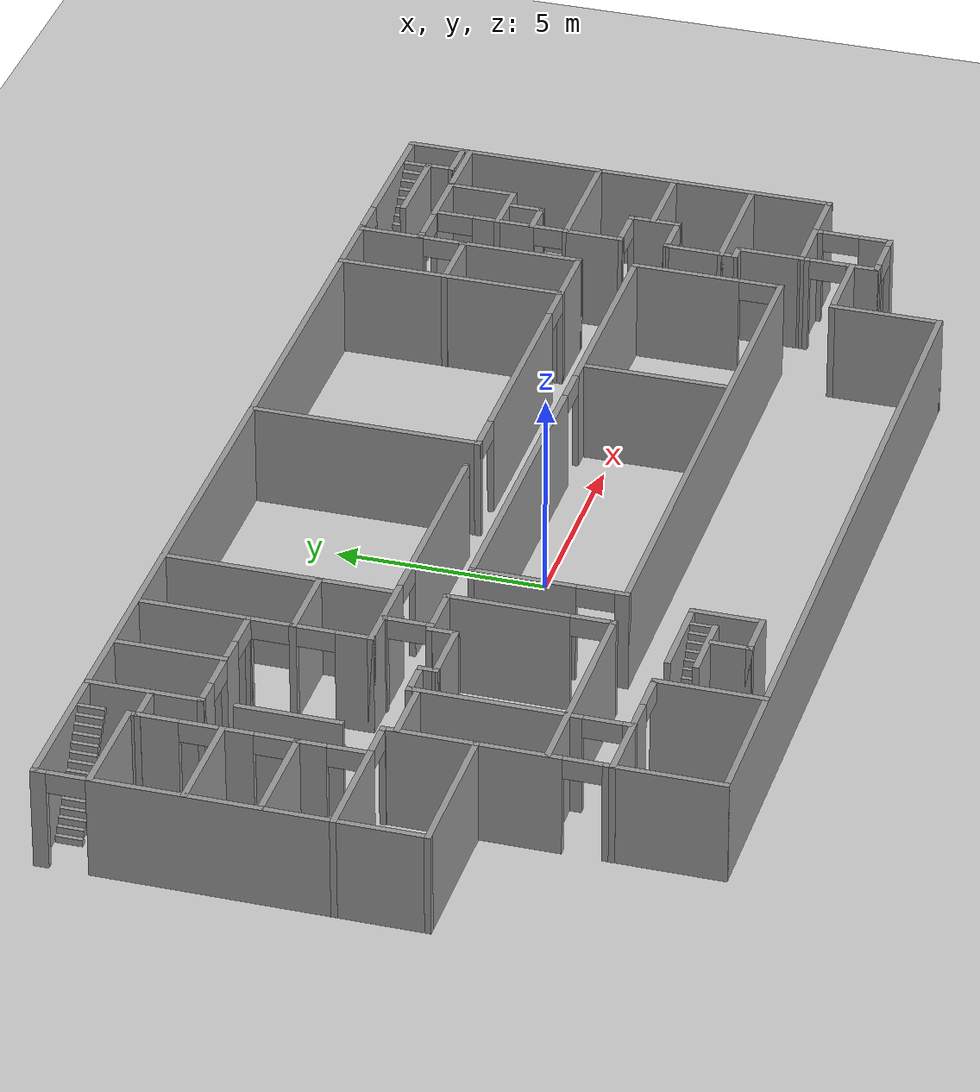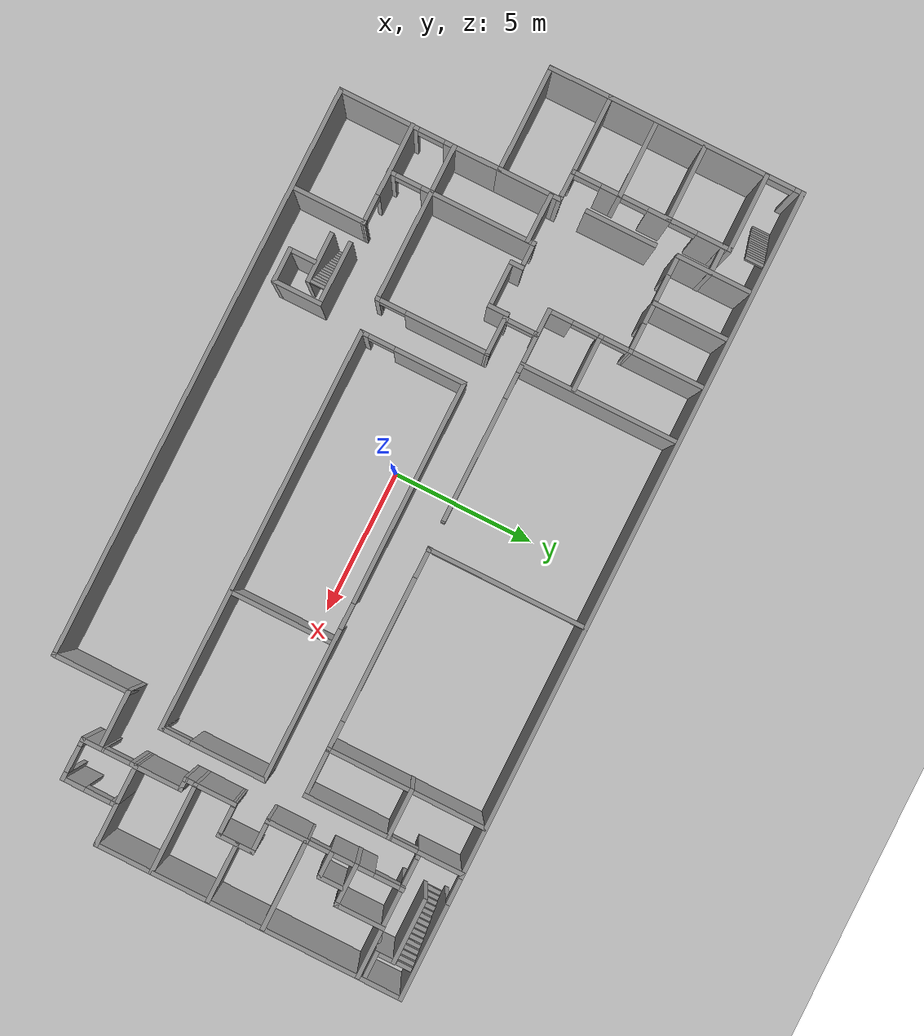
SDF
<sdf version="1.6">
 <world name="default">
  <light name="sun" type="directional">
   <pose>0 0 10 0 -0 0</pose>
   <diffuse>0.8 0.8 0.8 1</diffuse>
   <specular>0.1 0.1 0.1 1</specular>
   <attenuation>
    <range>1000</range>
    <constant>0.9</constant>
    <linear>0.01</linear>
    <quadratic>0.001</quadratic>
   </attenuation>
   <direction>-0.5 0.5 -1</direction>
  </light>
  <model name="ground_plane">
   <static>1</static>
   <link name="link">
    <collision name="collision">
     <geometry><plane><normal>0 0 1</normal><size>100 100</size></plane></geometry>
     <surface><friction><ode><mu>100</mu><mu2>50</mu2></ode></friction></surface>
    </collision>
    <visual name="visual">
     <cast_shadows>0</cast_shadows>
     <geometry><plane><normal>0 0 1</normal><size>100 100</size></plane></geometry>
     <material>
      <script><uri>file://media/materials/scripts/gazebo.material</uri><name>Gazebo/Grey</name></script>
     </material>
    </visual>
   </link>
  </model>
  <gravity>0 0 -9.8</gravity>
  <magnetic_field>6e-06 2.3e-05 -4.2e-05</magnetic_field>
  <atmosphere type="adiabatic"/>
  <physics name="default_physics" default="0" type="ode">
   <max_step_size>0.001</max_step_size>
   <real_time_factor>1</real_time_factor>
   <real_time_update_rate>1000</real_time_update_rate>
  </physics>
  <scene><ambient>0.4 0.4 0.4 1</ambient><background>0.7 0.7 0.7 1</background><shadows>1</shadows></scene>
  <spherical_coordinates>
   <surface_model>EARTH_WGS84</surface_model>
   <latitude_deg>0</latitude_deg>
   <longitude_deg>0</longitude_deg>
   <elevation>0</elevation>
   <heading_deg>0</heading_deg>
  </spherical_coordinates>
  <model name="deh_f1">
   <pose>0.520969 0.357811 0 0 -0 0</pose>
   <link name="Stairs_0">
    <visual name="Stairs_0_Visual_0">
     <pose>-6.2314 -5.10974 0.083333 0 -0 1.5708</pose>
     <geometry><box><size>0.49 0.113139 0.166667</size></box></geometry>
     <material>
      <script><uri>file://media/materials/scripts/gazebo.material</uri><name>Gazebo/Grey</name></script>
      <ambient>1 1 1 1</ambient>
     </material>
    </visual>
    <collision name="Stairs_0_Collision_0">
     <geometry><box><size>0.49 0.113139 0.166667</size></box></geometry>
     <pose>-6.2314 -5.10974 0.083333 0 -0 1.5708</pose>
    </collision>
    <visual name="Stairs_0_Visual_1">
     <pose>-6.11826 -5.10974 0.25 0 -0 1.5708</pose>
     <geometry><box><size>0.49 0.113139 0.166667</size></box></geometry>
     <material>
      <script><uri>file://media/materials/scripts/gazebo.material</uri><name>Gazebo/Grey</name></script>
      <ambient>1 1 1 1</ambient>
     </material>
    </visual>
    <collision name="Stairs_0_Collision_1">
     <geometry><box><size>0.49 0.113139 0.166667</size></box></geometry>
     <pose>-6.11826 -5.10974 0.25 0 -0 1.5708</pose>
    </collision>
    <visual name="Stairs_0_Visual_2">
     <pose>-6.00512 -5.10974 0.416667 0 -0 1.5708</pose>
     <geometry><box><size>0.49 0.113139 0.166667</size></box></geometry>
     <material>
      <script><uri>file://media/materials/scripts/gazebo.material</uri><name>Gazebo/Grey</name></script>
      <ambient>1 1 1 1</ambient>
     </material>
    </visual>
    <collision name="Stairs_0_Collision_2">
     <geometry><box><size>0.49 0.113139 0.166667</size></box></geometry>
     <pose>-6.00512 -5.10974 0.416667 0 -0 1.5708</pose>
    </collision>
    <visual name="Stairs_0_Visual_3">
     <pose>-5.89198 -5.10974 0.583333 0 -0 1.5708</pose>
     <geometry><box><size>0.49 0.113139 0.166667</size></box></geometry>
     <material>
      <script><uri>file://media/materials/scripts/gazebo.material</uri><name>Gazebo/Grey</name></script>
      <ambient>1 1 1 1</ambient>
     </material>
    </visual>
    <collision name="Stairs_0_Collision_3">
     <geometry><box><size>0.49 0.113139 0.166667</size></box></geometry>
     <pose>-5.89198 -5.10974 0.583333 0 -0 1.5708</pose>
    </collision>
    <visual name="Stairs_0_Visual_4">
     <pose>-5.77884 -5.10974 0.75 0 -0 1.5708</pose>
     <geometry><box><size>0.49 0.113139 0.166667</size></box></geometry>
     <material>
      <script><uri>file://media/materials/scripts/gazebo.material</uri><name>Gazebo/Grey</name></script>
      <ambient>1 1 1 1</ambient>
     </material>
    </visual>
    <collision name="Stairs_0_Collision_4">
     <geometry><box><size>0.49 0.113139 0.166667</size></box></geometry>
     <pose>-5.77884 -5.10974 0.75 0 -0 1.5708</pose>
    </collision>
    <visual name="Stairs_0_Visual_5">
     <pose>-5.66571 -5.10974 0.916667 0 -0 1.5708</pose>
     <geometry><box><size>0.49 0.113139 0.166667</size></box></geometry>
     <material>
      <script><uri>file://media/materials/scripts/gazebo.material</uri><name>Gazebo/Grey</name></script>
      <ambient>1 1 1 1</ambient>
     </material>
    </visual>
    <collision name="Stairs_0_Collision_5">
     <geometry><box><size>0.49 0.113139 0.166667</size></box></geometry>
     <pose>-5.66571 -5.10974 0.916667 0 -0 1.5708</pose>
    </collision>
    <visual name="Stairs_0_Visual_6">
     <pose>-5.55257 -5.10974 1.08333 0 -0 1.5708</pose>
     <geometry><box><size>0.49 0.113139 0.166667</size></box></geometry>
     <material>
      <script><uri>file://media/materials/scripts/gazebo.material</uri><name>Gazebo/Grey</name></script>
      <ambient>1 1 1 1</ambient>
     </material>
    </visual>
    <collision name="Stairs_0_Collision_6">
     <geometry><box><size>0.49 0.113139 0.166667</size></box></geometry>
     <pose>-5.55257 -5.10974 1.08333 0 -0 1.5708</pose>
    </collision>
    <visual name="Stairs_0_Visual_7">
     <pose>-5.43943 -5.10974 1.25 0 -0 1.5708</pose>
     <geometry><box><size>0.49 0.113139 0.166667</size></box></geometry>
     <material>
      <script><uri>file://media/materials/scripts/gazebo.material</uri><name>Gazebo/Grey</name></script>
      <ambient>1 1 1 1</ambient>
     </material>
    </visual>
    <collision name="Stairs_0_Collision_7">
     <geometry><box><size>0.49 0.113139 0.166667</size></box></geometry>
     <pose>-5.43943 -5.10974 1.25 0 -0 1.5708</pose>
    </collision>
    <visual name="Stairs_0_Visual_8">
     <pose>-5.32629 -5.10974 1.41667 0 -0 1.5708</pose>
     <geometry><box><size>0.49 0.113139 0.166667</size></box></geometry>
     <material>
      <script><uri>file://media/materials/scripts/gazebo.material</uri><name>Gazebo/Grey</name></script>
      <ambient>1 1 1 1</ambient>
     </material>
    </visual>
    <collision name="Stairs_0_Collision_8">
     <geometry><box><size>0.49 0.113139 0.166667</size></box></geometry>
     <pose>-5.32629 -5.10974 1.41667 0 -0 1.5708</pose>
    </collision>
    <visual name="Stairs_0_Visual_9">
     <pose>-5.21315 -5.10974 1.58333 0 -0 1.5708</pose>
     <geometry><box><size>0.49 0.113139 0.166667</size></box></geometry>
     <material>
      <script><uri>file://media/materials/scripts/gazebo.material</uri><name>Gazebo/Grey</name></script>
      <ambient>1 1 1 1</ambient>
     </material>
    </visual>
    <collision name="Stairs_0_Collision_9">
     <geometry><box><size>0.49 0.113139 0.166667</size></box></geometry>
     <pose>-5.21315 -5.10974 1.58333 0 -0 1.5708</pose>
    </collision>
    <visual name="Stairs_0_Visual_10">
     <pose>-5.10001 -5.10974 1.75 0 -0 1.5708</pose>
     <geometry><box><size>0.49 0.113139 0.166667</size></box></geometry>
     <material>
      <script><uri>file://media/materials/scripts/gazebo.material</uri><name>Gazebo/Grey</name></script>
      <ambient>1 1 1 1</ambient>
     </material>
    </visual>
    <collision name="Stairs_0_Collision_10">
     <geometry><box><size>0.49 0.113139 0.166667</size></box></geometry>
     <pose>-5.10001 -5.10974 1.75 0 -0 1.5708</pose>
    </collision>
    <visual name="Stairs_0_Visual_11">
     <pose>-4.98687 -5.10974 1.91667 0 -0 1.5708</pose>
     <geometry><box><size>0.49 0.113139 0.166667</size></box></geometry>
     <material>
      <script><uri>file://media/materials/scripts/gazebo.material</uri><name>Gazebo/Grey</name></script>
      <ambient>1 1 1 1</ambient>
     </material>
    </visual>
    <collision name="Stairs_0_Collision_11">
     <geometry><box><size>0.49 0.113139 0.166667</size></box></geometry>
     <pose>-4.98687 -5.10974 1.91667 0 -0 1.5708</pose>
    </collision>
    <visual name="Stairs_0_Visual_12">
     <pose>-4.87373 -5.10974 2.08333 0 -0 1.5708</pose>
     <geometry><box><size>0.49 0.113139 0.166667</size></box></geometry>
     <material>
      <script><uri>file://media/materials/scripts/gazebo.material</uri><name>Gazebo/Grey</name></script>
      <ambient>1 1 1 1</ambient>
     </material>
    </visual>
    <collision name="Stairs_0_Collision_12">
     <geometry><box><size>0.49 0.113139 0.166667</size></box></geometry>
     <pose>-4.87373 -5.10974 2.08333 0 -0 1.5708</pose>
    </collision>
    <visual name="Stairs_0_Visual_13">
     <pose>-4.76059 -5.10974 2.25 0 -0 1.5708</pose>
     <geometry><box><size>0.49 0.113139 0.166667</size></box></geometry>
     <material>
      <script><uri>file://media/materials/scripts/gazebo.material</uri><name>Gazebo/Grey</name></script>
      <ambient>1 1 1 1</ambient>
     </material>
    </visual>
    <collision name="Stairs_0_Collision_13">
     <geometry><box><size>0.49 0.113139 0.166667</size></box></geometry>
     <pose>-4.76059 -5.10974 2.25 0 -0 1.5708</pose>
    </collision>
    <visual name="Stairs_0_Visual_14">
     <pose>-4.64745 -5.10974 2.41667 0 -0 1.5708</pose>
     <geometry><box><size>0.49 0.113139 0.166667</size></box></geometry>
     <material>
      <script><uri>file://media/materials/scripts/gazebo.material</uri><name>Gazebo/Grey</name></script>
      <ambient>1 1 1 1</ambient>
     </material>
    </visual>
    <collision name="Stairs_0_Collision_14">
     <geometry><box><size>0.49 0.113139 0.166667</size></box></geometry>
     <pose>-4.64745 -5.10974 2.41667 0 -0 1.5708</pose>
    </collision>
   </link>
   <link name="Stairs_1">
    <visual name="Stairs_1_Visual_0">
     <pose>-13.1163 6.81612 0.083333 0 -0 1.5708</pose>
     <geometry><box><size>0.63499 0.119775 0.166667</size></box></geometry>
     <material>
      <script><uri>file://media/materials/scripts/gazebo.material</uri><name>Gazebo/Grey</name></script>
      <ambient>1 1 1 1</ambient>
     </material>
    </visual>
    <collision name="Stairs_1_Collision_0">
     <geometry><box><size>0.63499 0.119775 0.166667</size></box></geometry>
     <pose>-13.1163 6.81612 0.083333 0 -0 1.5708</pose>
    </collision>
    <visual name="Stairs_1_Visual_1">
     <pose>-12.9965 6.81612 0.25 0 -0 1.5708</pose>
     <geometry><box><size>0.63499 0.119775 0.166667</size></box></geometry>
     <material>
      <script><uri>file://media/materials/scripts/gazebo.material</uri><name>Gazebo/Grey</name></script>
      <ambient>1 1 1 1</ambient>
     </material>
    </visual>
    <collision name="Stairs_1_Collision_1">
     <geometry><box><size>0.63499 0.119775 0.166667</size></box></geometry>
     <pose>-12.9965 6.81612 0.25 0 -0 1.5708</pose>
    </collision>
    <visual name="Stairs_1_Visual_2">
     <pose>-12.8767 6.81612 0.416667 0 -0 1.5708</pose>
     <geometry><box><size>0.63499 0.119775 0.166667</size></box></geometry>
     <material>
      <script><uri>file://media/materials/scripts/gazebo.material</uri><name>Gazebo/Grey</name></script>
      <ambient>1 1 1 1</ambient>
     </material>
    </visual>
    <collision name="Stairs_1_Collision_2">
     <geometry><box><size>0.63499 0.119775 0.166667</size></box></geometry>
     <pose>-12.8767 6.81612 0.416667 0 -0 1.5708</pose>
    </collision>
    <visual name="Stairs_1_Visual_3">
     <pose>-12.757 6.81612 0.583333 0 -0 1.5708</pose>
     <geometry><box><size>0.63499 0.119775 0.166667</size></box></geometry>
     <material>
      <script><uri>file://media/materials/scripts/gazebo.material</uri><name>Gazebo/Grey</name></script>
      <ambient>1 1 1 1</ambient>
     </material>
    </visual>
    <collision name="Stairs_1_Collision_3">
     <geometry><box><size>0.63499 0.119775 0.166667</size></box></geometry>
     <pose>-12.757 6.81612 0.583333 0 -0 1.5708</pose>
    </collision>
    <visual name="Stairs_1_Visual_4">
     <pose>-12.6372 6.81612 0.75 0 -0 1.5708</pose>
     <geometry><box><size>0.63499 0.119775 0.166667</size></box></geometry>
     <material>
      <script><uri>file://media/materials/scripts/gazebo.material</uri><name>Gazebo/Grey</name></script>
      <ambient>1 1 1 1</ambient>
     </material>
    </visual>
    <collision name="Stairs_1_Collision_4">
     <geometry><box><size>0.63499 0.119775 0.166667</size></box></geometry>
     <pose>-12.6372 6.81612 0.75 0 -0 1.5708</pose>
    </collision>
    <visual name="Stairs_1_Visual_5">
     <pose>-12.5174 6.81612 0.916667 0 -0 1.5708</pose>
     <geometry><box><size>0.63499 0.119775 0.166667</size></box></geometry>
     <material>
      <script><uri>file://media/materials/scripts/gazebo.material</uri><name>Gazebo/Grey</name></script>
      <ambient>1 1 1 1</ambient>
     </material>
    </visual>
    <collision name="Stairs_1_Collision_5">
     <geometry><box><size>0.63499 0.119775 0.166667</size></box></geometry>
     <pose>-12.5174 6.81612 0.916667 0 -0 1.5708</pose>
    </collision>
    <visual name="Stairs_1_Visual_6">
     <pose>-12.3976 6.81612 1.08333 0 -0 1.5708</pose>
     <geometry><box><size>0.63499 0.119775 0.166667</size></box></geometry>
     <material>
      <script><uri>file://media/materials/scripts/gazebo.material</uri><name>Gazebo/Grey</name></script>
      <ambient>1 1 1 1</ambient>
     </material>
    </visual>
    <collision name="Stairs_1_Collision_6">
     <geometry><box><size>0.63499 0.119775 0.166667</size></box></geometry>
     <pose>-12.3976 6.81612 1.08333 0 -0 1.5708</pose>
    </collision>
    <visual name="Stairs_1_Visual_7">
     <pose>-12.2779 6.81612 1.25 0 -0 1.5708</pose>
     <geometry><box><size>0.63499 0.119775 0.166667</size></box></geometry>
     <material>
      <script><uri>file://media/materials/scripts/gazebo.material</uri><name>Gazebo/Grey</name></script>
      <ambient>1 1 1 1</ambient>
     </material>
    </visual>
    <collision name="Stairs_1_Collision_7">
     <geometry><box><size>0.63499 0.119775 0.166667</size></box></geometry>
     <pose>-12.2779 6.81612 1.25 0 -0 1.5708</pose>
    </collision>
    <visual name="Stairs_1_Visual_8">
     <pose>-12.1581 6.81612 1.41667 0 -0 1.5708</pose>
     <geometry><box><size>0.63499 0.119775 0.166667</size></box></geometry>
     <material>
      <script><uri>file://media/materials/scripts/gazebo.material</uri><name>Gazebo/Grey</name></script>
      <ambient>1 1 1 1</ambient>
     </material>
    </visual>
    <collision name="Stairs_1_Collision_8">
     <geometry><box><size>0.63499 0.119775 0.166667</size></box></geometry>
     <pose>-12.1581 6.81612 1.41667 0 -0 1.5708</pose>
    </collision>
    <visual name="Stairs_1_Visual_9">
     <pose>-12.0383 6.81612 1.58333 0 -0 1.5708</pose>
     <geometry><box><size>0.63499 0.119775 0.166667</size></box></geometry>
     <material>
      <script><uri>file://media/materials/scripts/gazebo.material</uri><name>Gazebo/Grey</name></script>
      <ambient>1 1 1 1</ambient>
     </material>
    </visual>
    <collision name="Stairs_1_Collision_9">
     <geometry><box><size>0.63499 0.119775 0.166667</size></box></geometry>
     <pose>-12.0383 6.81612 1.58333 0 -0 1.5708</pose>
    </collision>
    <visual name="Stairs_1_Visual_10">
     <pose>-11.9185 6.81612 1.75 0 -0 1.5708</pose>
     <geometry><box><size>0.63499 0.119775 0.166667</size></box></geometry>
     <material>
      <script><uri>file://media/materials/scripts/gazebo.material</uri><name>Gazebo/Grey</name></script>
      <ambient>1 1 1 1</ambient>
     </material>
    </visual>
    <collision name="Stairs_1_Collision_10">
     <geometry><box><size>0.63499 0.119775 0.166667</size></box></geometry>
     <pose>-11.9185 6.81612 1.75 0 -0 1.5708</pose>
    </collision>
    <visual name="Stairs_1_Visual_11">
     <pose>-11.7988 6.81612 1.91667 0 -0 1.5708</pose>
     <geometry><box><size>0.63499 0.119775 0.166667</size></box></geometry>
     <material>
      <script><uri>file://media/materials/scripts/gazebo.material</uri><name>Gazebo/Grey</name></script>
      <ambient>1 1 1 1</ambient>
     </material>
    </visual>
    <collision name="Stairs_1_Collision_11">
     <geometry><box><size>0.63499 0.119775 0.166667</size></box></geometry>
     <pose>-11.7988 6.81612 1.91667 0 -0 1.5708</pose>
    </collision>
    <visual name="Stairs_1_Visual_12">
     <pose>-11.679 6.81612 2.08333 0 -0 1.5708</pose>
     <geometry><box><size>0.63499 0.119775 0.166667</size></box></geometry>
     <material>
      <script><uri>file://media/materials/scripts/gazebo.material</uri><name>Gazebo/Grey</name></script>
      <ambient>1 1 1 1</ambient>
     </material>
    </visual>
    <collision name="Stairs_1_Collision_12">
     <geometry><box><size>0.63499 0.119775 0.166667</size></box></geometry>
     <pose>-11.679 6.81612 2.08333 0 -0 1.5708</pose>
    </collision>
    <visual name="Stairs_1_Visual_13">
     <pose>-11.5592 6.81612 2.25 0 -0 1.5708</pose>
     <geometry><box><size>0.63499 0.119775 0.166667</size></box></geometry>
     <material>
      <script><uri>file://media/materials/scripts/gazebo.material</uri><name>Gazebo/Grey</name></script>
      <ambient>1 1 1 1</ambient>
     </material>
    </visual>
    <collision name="Stairs_1_Collision_13">
     <geometry><box><size>0.63499 0.119775 0.166667</size></box></geometry>
     <pose>-11.5592 6.81612 2.25 0 -0 1.5708</pose>
    </collision>
    <visual name="Stairs_1_Visual_14">
     <pose>-11.4394 6.81612 2.41667 0 -0 1.5708</pose>
     <geometry><box><size>0.63499 0.119775 0.166667</size></box></geometry>
     <material>
      <script><uri>file://media/materials/scripts/gazebo.material</uri><name>Gazebo/Grey</name></script>
      <ambient>1 1 1 1</ambient>
     </material>
    </visual>
    <collision name="Stairs_1_Collision_14">
     <geometry><box><size>0.63499 0.119775 0.166667</size></box></geometry>
     <pose>-11.4394 6.81612 2.41667 0 -0 1.5708</pose>
    </collision>
   </link>
   <link name="Stairs_2">
    <visual name="Stairs_2_Visual_0">
     <pose>11.0741 6.86907 0.083333 0 -0 1.5708</pose>
     <geometry><box><size>0.520025 0.144952 0.166667</size></box></geometry>
     <material>
      <script><uri>file://media/materials/scripts/gazebo.material</uri><name>Gazebo/Grey</name></script>
      <ambient>1 1 1 1</ambient>
     </material>
    </visual>
    <collision name="Stairs_2_Collision_0">
     <geometry><box><size>0.520025 0.144952 0.166667</size></box></geometry>
     <pose>11.0741 6.86907 0.083333 0 -0 1.5708</pose>
    </collision>
    <visual name="Stairs_2_Visual_1">
     <pose>11.219 6.86907 0.25 0 -0 1.5708</pose>
     <geometry><box><size>0.520025 0.144952 0.166667</size></box></geometry>
     <material>
      <script><uri>file://media/materials/scripts/gazebo.material</uri><name>Gazebo/Grey</name></script>
      <ambient>1 1 1 1</ambient>
     </material>
    </visual>
    <collision name="Stairs_2_Collision_1">
     <geometry><box><size>0.520025 0.144952 0.166667</size></box></geometry>
     <pose>11.219 6.86907 0.25 0 -0 1.5708</pose>
    </collision>
    <visual name="Stairs_2_Visual_2">
     <pose>11.364 6.86907 0.416667 0 -0 1.5708</pose>
     <geometry><box><size>0.520025 0.144952 0.166667</size></box></geometry>
     <material>
      <script><uri>file://media/materials/scripts/gazebo.material</uri><name>Gazebo/Grey</name></script>
      <ambient>1 1 1 1</ambient>
     </material>
    </visual>
    <collision name="Stairs_2_Collision_2">
     <geometry><box><size>0.520025 0.144952 0.166667</size></box></geometry>
     <pose>11.364 6.86907 0.416667 0 -0 1.5708</pose>
    </collision>
    <visual name="Stairs_2_Visual_3">
     <pose>11.5089 6.86907 0.583333 0 -0 1.5708</pose>
     <geometry><box><size>0.520025 0.144952 0.166667</size></box></geometry>
     <material>
      <script><uri>file://media/materials/scripts/gazebo.material</uri><name>Gazebo/Grey</name></script>
      <ambient>1 1 1 1</ambient>
     </material>
    </visual>
    <collision name="Stairs_2_Collision_3">
     <geometry><box><size>0.520025 0.144952 0.166667</size></box></geometry>
     <pose>11.5089 6.86907 0.583333 0 -0 1.5708</pose>
    </collision>
    <visual name="Stairs_2_Visual_4">
     <pose>11.6539 6.86907 0.75 0 -0 1.5708</pose>
     <geometry><box><size>0.520025 0.144952 0.166667</size></box></geometry>
     <material>
      <script><uri>file://media/materials/scripts/gazebo.material</uri><name>Gazebo/Grey</name></script>
      <ambient>1 1 1 1</ambient>
     </material>
    </visual>
    <collision name="Stairs_2_Collision_4">
     <geometry><box><size>0.520025 0.144952 0.166667</size></box></geometry>
     <pose>11.6539 6.86907 0.75 0 -0 1.5708</pose>
    </collision>
    <visual name="Stairs_2_Visual_5">
     <pose>11.7988 6.86907 0.916667 0 -0 1.5708</pose>
     <geometry><box><size>0.520025 0.144952 0.166667</size></box></geometry>
     <material>
      <script><uri>file://media/materials/scripts/gazebo.material</uri><name>Gazebo/Grey</name></script>
      <ambient>1 1 1 1</ambient>
     </material>
    </visual>
    <collision name="Stairs_2_Collision_5">
     <geometry><box><size>0.520025 0.144952 0.166667</size></box></geometry>
     <pose>11.7988 6.86907 0.916667 0 -0 1.5708</pose>
    </collision>
    <visual name="Stairs_2_Visual_6">
     <pose>11.9438 6.86907 1.08333 0 -0 1.5708</pose>
     <geometry><box><size>0.520025 0.144952 0.166667</size></box></geometry>
     <material>
      <script><uri>file://media/materials/scripts/gazebo.material</uri><name>Gazebo/Grey</name></script>
      <ambient>1 1 1 1</ambient>
     </material>
    </visual>
    <collision name="Stairs_2_Collision_6">
     <geometry><box><size>0.520025 0.144952 0.166667</size></box></geometry>
     <pose>11.9438 6.86907 1.08333 0 -0 1.5708</pose>
    </collision>
    <visual name="Stairs_2_Visual_7">
     <pose>12.0887 6.86907 1.25 0 -0 1.5708</pose>
     <geometry><box><size>0.520025 0.144952 0.166667</size></box></geometry>
     <material>
      <script><uri>file://media/materials/scripts/gazebo.material</uri><name>Gazebo/Grey</name></script>
      <ambient>1 1 1 1</ambient>
     </material>
    </visual>
    <collision name="Stairs_2_Collision_7">
     <geometry><box><size>0.520025 0.144952 0.166667</size></box></geometry>
     <pose>12.0887 6.86907 1.25 0 -0 1.5708</pose>
    </collision>
    <visual name="Stairs_2_Visual_8">
     <pose>12.2337 6.86907 1.41667 0 -0 1.5708</pose>
     <geometry><box><size>0.520025 0.144952 0.166667</size></box></geometry>
     <material>
      <script><uri>file://media/materials/scripts/gazebo.material</uri><name>Gazebo/Grey</name></script>
      <ambient>1 1 1 1</ambient>
     </material>
    </visual>
    <collision name="Stairs_2_Collision_8">
     <geometry><box><size>0.520025 0.144952 0.166667</size></box></geometry>
     <pose>12.2337 6.86907 1.41667 0 -0 1.5708</pose>
    </collision>
    <visual name="Stairs_2_Visual_9">
     <pose>12.3786 6.86907 1.58333 0 -0 1.5708</pose>
     <geometry><box><size>0.520025 0.144952 0.166667</size></box></geometry>
     <material>
      <script><uri>file://media/materials/scripts/gazebo.material</uri><name>Gazebo/Grey</name></script>
      <ambient>1 1 1 1</ambient>
     </material>
    </visual>
    <collision name="Stairs_2_Collision_9">
     <geometry><box><size>0.520025 0.144952 0.166667</size></box></geometry>
     <pose>12.3786 6.86907 1.58333 0 -0 1.5708</pose>
    </collision>
    <visual name="Stairs_2_Visual_10">
     <pose>12.5236 6.86907 1.75 0 -0 1.5708</pose>
     <geometry><box><size>0.520025 0.144952 0.166667</size></box></geometry>
     <material>
      <script><uri>file://media/materials/scripts/gazebo.material</uri><name>Gazebo/Grey</name></script>
      <ambient>1 1 1 1</ambient>
     </material>
    </visual>
    <collision name="Stairs_2_Collision_10">
     <geometry><box><size>0.520025 0.144952 0.166667</size></box></geometry>
     <pose>12.5236 6.86907 1.75 0 -0 1.5708</pose>
    </collision>
    <visual name="Stairs_2_Visual_11">
     <pose>12.6685 6.86907 1.91667 0 -0 1.5708</pose>
     <geometry><box><size>0.520025 0.144952 0.166667</size></box></geometry>
     <material>
      <script><uri>file://media/materials/scripts/gazebo.material</uri><name>Gazebo/Grey</name></script>
      <ambient>1 1 1 1</ambient>
     </material>
    </visual>
    <collision name="Stairs_2_Collision_11">
     <geometry><box><size>0.520025 0.144952 0.166667</size></box></geometry>
     <pose>12.6685 6.86907 1.91667 0 -0 1.5708</pose>
    </collision>
    <visual name="Stairs_2_Visual_12">
     <pose>12.8135 6.86907 2.08333 0 -0 1.5708</pose>
     <geometry><box><size>0.520025 0.144952 0.166667</size></box></geometry>
     <material>
      <script><uri>file://media/materials/scripts/gazebo.material</uri><name>Gazebo/Grey</name></script>
      <ambient>1 1 1 1</ambient>
     </material>
    </visual>
    <collision name="Stairs_2_Collision_12">
     <geometry><box><size>0.520025 0.144952 0.166667</size></box></geometry>
     <pose>12.8135 6.86907 2.08333 0 -0 1.5708</pose>
    </collision>
    <visual name="Stairs_2_Visual_13">
     <pose>12.9584 6.86907 2.25 0 -0 1.5708</pose>
     <geometry><box><size>0.520025 0.144952 0.166667</size></box></geometry>
     <material>
      <script><uri>file://media/materials/scripts/gazebo.material</uri><name>Gazebo/Grey</name></script>
      <ambient>1 1 1 1</ambient>
     </material>
    </visual>
    <collision name="Stairs_2_Collision_13">
     <geometry><box><size>0.520025 0.144952 0.166667</size></box></geometry>
     <pose>12.9584 6.86907 2.25 0 -0 1.5708</pose>
    </collision>
    <visual name="Stairs_2_Visual_14">
     <pose>13.1034 6.86907 2.41667 0 -0 1.5708</pose>
     <geometry><box><size>0.520025 0.144952 0.166667</size></box></geometry>
     <material>
      <script><uri>file://media/materials/scripts/gazebo.material</uri><name>Gazebo/Grey</name></script>
      <ambient>1 1 1 1</ambient>
     </material>
    </visual>
    <collision name="Stairs_2_Collision_14">
     <geometry><box><size>0.520025 0.144952 0.166667</size></box></geometry>
     <pose>13.1034 6.86907 2.41667 0 -0 1.5708</pose>
    </collision>
   </link>
   <link name="Wall_0">
    <collision name="Wall_0_Collision">
     <geometry><box><size>20 0.15 2.5</size></box></geometry>
     <pose>0 0 1.25 0 -0 0</pose>
    </collision>
    <visual name="Wall_0_Visual">
     <pose>0 0 1.25 0 -0 0</pose>
     <geometry><box><size>20 0.15 2.5</size></box></geometry>
     <material>
      <script><uri>file://media/materials/scripts/gazebo.material</uri><name>Gazebo/Grey</name></script>
      <ambient>1 1 1 1</ambient>
     </material>
    </visual>
    <pose>-0.526964 -7.22647 0 0 -0 0</pose>
   </link>
   <link name="Wall_10">
    <collision name="Wall_10_Collision">
     <geometry><box><size>0.75 0.15 2.5</size></box></geometry>
     <pose>0 0 1.25 0 -0 0</pose>
    </collision>
    <visual name="Wall_10_Visual">
     <pose>0 0 1.25 0 -0 0</pose>
     <geometry><box><size>0.75 0.15 2.5</size></box></geometry>
     <material>
      <script><uri>file://media/materials/scripts/gazebo.material</uri><name>Gazebo/Grey</name></script>
      <ambient>1 1 1 1</ambient>
     </material>
    </visual>
    <pose>11.348 -4.92647 0 0 -0 1.5708</pose>
   </link>
   <link name="Wall_101">
    <collision name="Wall_101_Collision">
     <geometry><box><size>5.6204 0.15 2.5</size></box></geometry>
     <pose>0 0 1.25 0 -0 0</pose>
    </collision>
    <visual name="Wall_101_Visual">
     <pose>0 0 1.25 0 -0 0</pose>
     <geometry><box><size>5.6204 0.15 2.5</size></box></geometry>
     <material>
      <script><uri>file://media/materials/scripts/gazebo.material</uri><name>Gazebo/Grey</name></script>
      <ambient>1 1 1 1</ambient>
     </material>
    </visual>
    <pose>-5.26917 4.49123 0 0 -0 1.57128</pose>
   </link>
   <link name="Wall_103">
    <collision name="Wall_103_Collision">
     <geometry><box><size>2 0.15 2.5</size></box></geometry>
     <pose>0 0 1.25 0 -0 0</pose>
    </collision>
    <visual name="Wall_103_Visual">
     <pose>0 0 1.25 0 -0 0</pose>
     <geometry><box><size>2 0.15 2.5</size></box></geometry>
     <material>
      <script><uri>file://media/materials/scripts/gazebo.material</uri><name>Gazebo/Grey</name></script>
      <ambient>1 1 1 1</ambient>
     </material>
    </visual>
    <pose>-6.238 3.5569 0 0 -0 0</pose>
   </link>
   <link name="Wall_105">
    <pose>-10.9717 5.7489 0 0 -0 3.14159</pose>
    <visual name="Wall_105_Visual_0">
     <pose>-0.453629 0 1.25 0 -0 0</pose>
     <geometry><box><size>0.165238 0.15 2.5</size></box></geometry>
     <material>
      <script><uri>file://media/materials/scripts/gazebo.material</uri><name>Gazebo/Grey</name></script>
      <ambient>1 1 1 1</ambient>
     </material>
    </visual>
    <collision name="Wall_105_Collision_0">
     <geometry><box><size>0.165238 0.15 2.5</size></box></geometry>
     <pose>-0.453629 0 1.25 0 -0 0</pose>
    </collision>
    <visual name="Wall_105_Visual_1">
     <pose>0.457005 0 1.25 0 -0 0</pose>
     <geometry><box><size>0.158486 0.15 2.5</size></box></geometry>
     <material>
      <script><uri>file://media/materials/scripts/gazebo.material</uri><name>Gazebo/Grey</name></script>
      <ambient>1 1 1 1</ambient>
     </material>
    </visual>
    <collision name="Wall_105_Collision_1">
     <geometry><box><size>0.158486 0.15 2.5</size></box></geometry>
     <pose>0.457005 0 1.25 0 -0 0</pose>
    </collision>
    <visual name="Wall_105_Visual_2">
     <pose>0.003376 0 2.25 0 -0 0</pose>
     <geometry><box><size>0.748771 0.15 0.5</size></box></geometry>
     <material>
      <script><uri>file://media/materials/scripts/gazebo.material</uri><name>Gazebo/Grey</name></script>
      <ambient>1 1 1 1</ambient>
     </material>
    </visual>
    <collision name="Wall_105_Collision_2">
     <geometry><box><size>0.748771 0.15 0.5</size></box></geometry>
     <pose>0.003376 0 2.25 0 -0 0</pose>
    </collision>
   </link>
   <link name="Wall_107">
    <collision name="Wall_107_Collision">
     <geometry><box><size>5.62515 0.15 2.5</size></box></geometry>
     <pose>0 0 1.25 0 -0 0</pose>
    </collision>
    <visual name="Wall_107_Visual">
     <pose>0 0 1.25 0 -0 0</pose>
     <geometry><box><size>5.62515 0.15 2.5</size></box></geometry>
     <material>
      <script><uri>file://media/materials/scripts/gazebo.material</uri><name>Gazebo/Grey</name></script>
      <ambient>1 1 1 1</ambient>
     </material>
    </visual>
    <pose>1.21165 4.48247 0 0 0 -1.5708</pose>
   </link>
   <link name="Wall_109">
    <collision name="Wall_109_Collision">
     <geometry><box><size>1.75 0.15 2.5</size></box></geometry>
     <pose>0 0 1.25 0 -0 0</pose>
    </collision>
    <visual name="Wall_109_Visual">
     <pose>0 0 1.25 0 -0 0</pose>
     <geometry><box><size>1.75 0.15 2.5</size></box></geometry>
     <material>
      <script><uri>file://media/materials/scripts/gazebo.material</uri><name>Gazebo/Grey</name></script>
      <ambient>1 1 1 1</ambient>
     </material>
    </visual>
    <pose>8.97986 1.75239 0 0 -0 0</pose>
   </link>
   <link name="Wall_110">
    <pose>9.77348 4.47484 0 0 -0 1.57314</pose>
    <visual name="Wall_110_Visual_0">
     <pose>-1.26286 0 1.25 0 -0 0</pose>
     <geometry><box><size>3.06917 0.15 2.5</size></box></geometry>
     <material>
      <script><uri>file://media/materials/scripts/gazebo.material</uri><name>Gazebo/Grey</name></script>
      <ambient>1 1 1 1</ambient>
     </material>
    </visual>
    <collision name="Wall_110_Collision_0">
     <geometry><box><size>3.06917 0.15 2.5</size></box></geometry>
     <pose>-1.26286 0 1.25 0 -0 0</pose>
    </collision>
    <visual name="Wall_110_Visual_1">
     <pose>1.98459 0 1.25 0 -0 0</pose>
     <geometry><box><size>1.62573 0.15 2.5</size></box></geometry>
     <material>
      <script><uri>file://media/materials/scripts/gazebo.material</uri><name>Gazebo/Grey</name></script>
      <ambient>1 1 1 1</ambient>
     </material>
    </visual>
    <collision name="Wall_110_Collision_1">
     <geometry><box><size>1.62573 0.15 2.5</size></box></geometry>
     <pose>1.98459 0 1.25 0 -0 0</pose>
    </collision>
    <visual name="Wall_110_Visual_2">
     <pose>0.721725 0 2.25 0 -0 0</pose>
     <geometry><box><size>0.9 0.15 0.5</size></box></geometry>
     <material>
      <script><uri>file://media/materials/scripts/gazebo.material</uri><name>Gazebo/Grey</name></script>
      <ambient>1 1 1 1</ambient>
     </material>
    </visual>
    <collision name="Wall_110_Collision_2">
     <geometry><box><size>0.9 0.15 0.5</size></box></geometry>
     <pose>0.721725 0 2.25 0 -0 0</pose>
    </collision>
   </link>
   <link name="Wall_114">
    <pose>11.9124 5.72672 0 0 -0 0</pose>
    <visual name="Wall_114_Visual_0">
     <pose>-2.0611 0 1.25 0 -0 0</pose>
     <geometry><box><size>0.273024 0.15 2.5</size></box></geometry>
     <material>
      <script><uri>file://media/materials/scripts/gazebo.material</uri><name>Gazebo/Grey</name></script>
      <ambient>1 1 1 1</ambient>
     </material>
    </visual>
    <collision name="Wall_114_Collision_0">
     <geometry><box><size>0.273024 0.15 2.5</size></box></geometry>
     <pose>-2.0611 0 1.25 0 -0 0</pose>
    </collision>
    <visual name="Wall_114_Visual_1">
     <pose>0.586512 0 1.25 0 -0 0</pose>
     <geometry><box><size>3.2222 0.15 2.5</size></box></geometry>
     <material>
      <script><uri>file://media/materials/scripts/gazebo.material</uri><name>Gazebo/Grey</name></script>
      <ambient>1 1 1 1</ambient>
     </material>
    </visual>
    <collision name="Wall_114_Collision_1">
     <geometry><box><size>3.2222 0.15 2.5</size></box></geometry>
     <pose>0.586512 0 1.25 0 -0 0</pose>
    </collision>
    <visual name="Wall_114_Visual_2">
     <pose>-1.47459 0 2.25 0 -0 0</pose>
     <geometry><box><size>0.9 0.15 0.5</size></box></geometry>
     <material>
      <script><uri>file://media/materials/scripts/gazebo.material</uri><name>Gazebo/Grey</name></script>
      <ambient>1 1 1 1</ambient>
     </material>
    </visual>
    <collision name="Wall_114_Collision_2">
     <geometry><box><size>0.9 0.15 0.5</size></box></geometry>
     <pose>-1.47459 0 2.25 0 -0 0</pose>
    </collision>
   </link>
   <link name="Wall_116">
    <pose>11.0229 4.08144 0 0 0 -1.5708</pose>
    <visual name="Wall_116_Visual_0">
     <pose>-1.65988 0 1.25 0 -0 0</pose>
     <geometry><box><size>0.160376 0.15 2.5</size></box></geometry>
     <material>
      <script><uri>file://media/materials/scripts/gazebo.material</uri><name>Gazebo/Grey</name></script>
      <ambient>1 1 1 1</ambient>
     </material>
    </visual>
    <collision name="Wall_116_Collision_0">
     <geometry><box><size>0.160376 0.15 2.5</size></box></geometry>
     <pose>-1.65988 0 1.25 0 -0 0</pose>
    </collision>
    <visual name="Wall_116_Visual_1">
     <pose>0.093656 0 1.25 0 -0 0</pose>
     <geometry><box><size>1.54669 0.15 2.5</size></box></geometry>
     <material>
      <script><uri>file://media/materials/scripts/gazebo.material</uri><name>Gazebo/Grey</name></script>
      <ambient>1 1 1 1</ambient>
     </material>
    </visual>
    <collision name="Wall_116_Collision_1">
     <geometry><box><size>1.54669 0.15 2.5</size></box></geometry>
     <pose>0.093656 0 1.25 0 -0 0</pose>
    </collision>
    <visual name="Wall_116_Visual_2">
     <pose>1.66388 0 1.25 0 -0 0</pose>
     <geometry><box><size>0.152369 0.15 2.5</size></box></geometry>
     <material>
      <script><uri>file://media/materials/scripts/gazebo.material</uri><name>Gazebo/Grey</name></script>
      <ambient>1 1 1 1</ambient>
     </material>
    </visual>
    <collision name="Wall_116_Collision_2">
     <geometry><box><size>0.152369 0.15 2.5</size></box></geometry>
     <pose>1.66388 0 1.25 0 -0 0</pose>
    </collision>
    <visual name="Wall_116_Visual_3">
     <pose>-1.12969 0 2.25 0 -0 0</pose>
     <geometry><box><size>0.9 0.15 0.5</size></box></geometry>
     <material>
      <script><uri>file://media/materials/scripts/gazebo.material</uri><name>Gazebo/Grey</name></script>
      <ambient>1 1 1 1</ambient>
     </material>
    </visual>
    <collision name="Wall_116_Collision_3">
     <geometry><box><size>0.9 0.15 0.5</size></box></geometry>
     <pose>-1.12969 0 2.25 0 -0 0</pose>
    </collision>
    <visual name="Wall_116_Visual_4">
     <pose>1.22735 0 2.25 0 -0 0</pose>
     <geometry><box><size>0.720696 0.15 0.5</size></box></geometry>
     <material>
      <script><uri>file://media/materials/scripts/gazebo.material</uri><name>Gazebo/Grey</name></script>
      <ambient>1 1 1 1</ambient>
     </material>
    </visual>
    <collision name="Wall_116_Collision_4">
     <geometry><box><size>0.720696 0.15 0.5</size></box></geometry>
     <pose>1.22735 0 2.25 0 -0 0</pose>
    </collision>
   </link>
   <link name="Wall_117">
    <collision name="Wall_117_Collision">
     <geometry><box><size>3.16787 0.15 2.5</size></box></geometry>
     <pose>0 0 1.25 0 -0 0</pose>
    </collision>
    <visual name="Wall_117_Visual">
     <pose>0 0 1.25 0 -0 0</pose>
     <geometry><box><size>3.16787 0.15 2.5</size></box></geometry>
     <material>
      <script><uri>file://media/materials/scripts/gazebo.material</uri><name>Gazebo/Grey</name></script>
      <ambient>1 1 1 1</ambient>
     </material>
    </visual>
    <pose>12.5218 2.4204 0 0 -0 0.002627</pose>
   </link>
   <link name="Wall_119">
    <collision name="Wall_119_Collision">
     <geometry><box><size>1.5 0.15 2.5</size></box></geometry>
     <pose>0 0 1.25 0 -0 0</pose>
    </collision>
    <visual name="Wall_119_Visual">
     <pose>0 0 1.25 0 -0 0</pose>
     <geometry><box><size>1.5 0.15 2.5</size></box></geometry>
     <material>
      <script><uri>file://media/materials/scripts/gazebo.material</uri><name>Gazebo/Grey</name></script>
      <ambient>1 1 1 1</ambient>
     </material>
    </visual>
    <pose>11.6872 4.13684 0 0 -0 0</pose>
   </link>
   <link name="Wall_12">
    <collision name="Wall_12_Collision">
     <geometry><box><size>2.75 0.15 2.5</size></box></geometry>
     <pose>0 0 1.25 0 -0 0</pose>
    </collision>
    <visual name="Wall_12_Visual">
     <pose>0 0 1.25 0 -0 0</pose>
     <geometry><box><size>2.75 0.15 2.5</size></box></geometry>
     <material>
      <script><uri>file://media/materials/scripts/gazebo.material</uri><name>Gazebo/Grey</name></script>
      <ambient>1 1 1 1</ambient>
     </material>
    </visual>
    <pose>9.39804 -5.92647 0 0 -0 1.5708</pose>
   </link>
   <link name="Wall_120">
    <collision name="Wall_120_Collision">
     <geometry><box><size>1.75 0.15 2.5</size></box></geometry>
     <pose>0 0 1.25 0 -0 0</pose>
    </collision>
    <visual name="Wall_120_Visual">
     <pose>0 0 1.25 0 -0 0</pose>
     <geometry><box><size>1.75 0.15 2.5</size></box></geometry>
     <material>
      <script><uri>file://media/materials/scripts/gazebo.material</uri><name>Gazebo/Grey</name></script>
      <ambient>1 1 1 1</ambient>
     </material>
    </visual>
    <pose>12.3622 4.93684 0 0 -0 1.5708</pose>
   </link>
   <link name="Wall_122">
    <collision name="Wall_122_Collision">
     <geometry><box><size>1 0.15 2.5</size></box></geometry>
     <pose>0 0 1.25 0 -0 0</pose>
    </collision>
    <visual name="Wall_122_Visual">
     <pose>0 0 1.25 0 -0 0</pose>
     <geometry><box><size>1 0.15 2.5</size></box></geometry>
     <material>
      <script><uri>file://media/materials/scripts/gazebo.material</uri><name>Gazebo/Grey</name></script>
      <ambient>1 1 1 1</ambient>
     </material>
    </visual>
    <pose>11.8301 3.70041 0 0 0 -1.5708</pose>
   </link>
   <link name="Wall_123">
    <collision name="Wall_123_Collision">
     <geometry><box><size>0.951518 0.15 2.5</size></box></geometry>
     <pose>0 0 1.25 0 -0 0</pose>
    </collision>
    <visual name="Wall_123_Visual">
     <pose>0 0 1.25 0 -0 0</pose>
     <geometry><box><size>0.951518 0.15 2.5</size></box></geometry>
     <material>
      <script><uri>file://media/materials/scripts/gazebo.material</uri><name>Gazebo/Grey</name></script>
      <ambient>1 1 1 1</ambient>
     </material>
    </visual>
    <pose>11.4294 3.27697 0 0 -0 3.1377</pose>
   </link>
   <link name="Wall_125">
    <collision name="Wall_125_Collision">
     <geometry><box><size>1.75 0.15 2.5</size></box></geometry>
     <pose>0 0 1.25 0 -0 0</pose>
    </collision>
    <visual name="Wall_125_Visual">
     <pose>0 0 1.25 0 -0 0</pose>
     <geometry><box><size>1.75 0.15 2.5</size></box></geometry>
     <material>
      <script><uri>file://media/materials/scripts/gazebo.material</uri><name>Gazebo/Grey</name></script>
      <ambient>1 1 1 1</ambient>
     </material>
    </visual>
    <pose>8.97011 4.62775 0 0 -0 3.14159</pose>
   </link>
   <link name="Wall_127">
    <collision name="Wall_127_Collision">
     <geometry><box><size>14 0.15 2.5</size></box></geometry>
     <pose>0 0 1.25 0 -0 0</pose>
    </collision>
    <visual name="Wall_127_Visual">
     <pose>0 0 1.25 0 -0 0</pose>
     <geometry><box><size>14 0.15 2.5</size></box></geometry>
     <material>
      <script><uri>file://media/materials/scripts/gazebo.material</uri><name>Gazebo/Grey</name></script>
      <ambient>1 1 1 1</ambient>
     </material>
    </visual>
    <pose>3.00654 -3.2072 0 0 -0 0</pose>
   </link>
   <link name="Wall_128">
    <pose>9.93154 -1.4072 0 0 -0 1.5708</pose>
    <visual name="Wall_128_Visual_0">
     <pose>-1.78467 0 1.25 0 -0 0</pose>
     <geometry><box><size>0.180652 0.15 2.5</size></box></geometry>
     <material>
      <script><uri>file://media/materials/scripts/gazebo.material</uri><name>Gazebo/Grey</name></script>
      <ambient>1 1 1 1</ambient>
     </material>
    </visual>
    <collision name="Wall_128_Collision_0">
     <geometry><box><size>0.180652 0.15 2.5</size></box></geometry>
     <pose>-1.78467 0 1.25 0 -0 0</pose>
    </collision>
    <visual name="Wall_128_Visual_1">
     <pose>0.540326 0 1.25 0 -0 0</pose>
     <geometry><box><size>2.66935 0.15 2.5</size></box></geometry>
     <material>
      <script><uri>file://media/materials/scripts/gazebo.material</uri><name>Gazebo/Grey</name></script>
      <ambient>1 1 1 1</ambient>
     </material>
    </visual>
    <collision name="Wall_128_Collision_1">
     <geometry><box><size>2.66935 0.15 2.5</size></box></geometry>
     <pose>0.540326 0 1.25 0 -0 0</pose>
    </collision>
    <visual name="Wall_128_Visual_2">
     <pose>-1.24435 0 2.25 0 -0 0</pose>
     <geometry><box><size>0.9 0.15 0.5</size></box></geometry>
     <material>
      <script><uri>file://media/materials/scripts/gazebo.material</uri><name>Gazebo/Grey</name></script>
      <ambient>1 1 1 1</ambient>
     </material>
    </visual>
    <collision name="Wall_128_Collision_2">
     <geometry><box><size>0.9 0.15 0.5</size></box></geometry>
     <pose>-1.24435 0 2.25 0 -0 0</pose>
    </collision>
   </link>
   <link name="Wall_129">
    <pose>3.00654 0.392797 0 0 -0 3.14159</pose>
    <visual name="Wall_129_Visual_0">
     <pose>-4.33483 0 1.25 0 -0 0</pose>
     <geometry><box><size>5.33035 0.15 2.5</size></box></geometry>
     <material>
      <script><uri>file://media/materials/scripts/gazebo.material</uri><name>Gazebo/Grey</name></script>
      <ambient>1 1 1 1</ambient>
     </material>
    </visual>
    <collision name="Wall_129_Collision_0">
     <geometry><box><size>5.33035 0.15 2.5</size></box></geometry>
     <pose>-4.33483 0 1.25 0 -0 0</pose>
    </collision>
    <visual name="Wall_129_Visual_1">
     <pose>3.11517 0 1.25 0 -0 0</pose>
     <geometry><box><size>7.76965 0.15 2.5</size></box></geometry>
     <material>
      <script><uri>file://media/materials/scripts/gazebo.material</uri><name>Gazebo/Grey</name></script>
      <ambient>1 1 1 1</ambient>
     </material>
    </visual>
    <collision name="Wall_129_Collision_1">
     <geometry><box><size>7.76965 0.15 2.5</size></box></geometry>
     <pose>3.11517 0 1.25 0 -0 0</pose>
    </collision>
    <visual name="Wall_129_Visual_2">
     <pose>-1.21965 0 2.25 0 -0 0</pose>
     <geometry><box><size>0.9 0.15 0.5</size></box></geometry>
     <material>
      <script><uri>file://media/materials/scripts/gazebo.material</uri><name>Gazebo/Grey</name></script>
      <ambient>1 1 1 1</ambient>
     </material>
    </visual>
    <collision name="Wall_129_Collision_2">
     <geometry><box><size>0.9 0.15 0.5</size></box></geometry>
     <pose>-1.21965 0 2.25 0 -0 0</pose>
    </collision>
   </link>
   <link name="Wall_13">
    <collision name="Wall_13_Collision">
     <geometry><box><size>2.1 0.15 2.5</size></box></geometry>
     <pose>0 0 1.25 0 -0 0</pose>
    </collision>
    <visual name="Wall_13_Visual">
     <pose>0 0 1.25 0 -0 0</pose>
     <geometry><box><size>2.1 0.15 2.5</size></box></geometry>
     <material>
      <script><uri>file://media/materials/scripts/gazebo.material</uri><name>Gazebo/Grey</name></script>
      <ambient>1 1 1 1</ambient>
     </material>
    </visual>
    <pose>10.373 -4.62647 0 0 -0 0</pose>
   </link>
   <link name="Wall_130">
    <pose>-3.91846 -1.4072 0 0 0 -1.5708</pose>
    <visual name="Wall_130_Visual_0">
     <pose>-0.617959 0 1.25 0 -0 0</pose>
     <geometry><box><size>2.51408 0.15 2.5</size></box></geometry>
     <material>
      <script><uri>file://media/materials/scripts/gazebo.material</uri><name>Gazebo/Grey</name></script>
      <ambient>1 1 1 1</ambient>
     </material>
    </visual>
    <collision name="Wall_130_Collision_0">
     <geometry><box><size>2.51408 0.15 2.5</size></box></geometry>
     <pose>-0.617959 0 1.25 0 -0 0</pose>
    </collision>
    <visual name="Wall_130_Visual_1">
     <pose>1.70704 0 1.25 0 -0 0</pose>
     <geometry><box><size>0.335919 0.15 2.5</size></box></geometry>
     <material>
      <script><uri>file://media/materials/scripts/gazebo.material</uri><name>Gazebo/Grey</name></script>
      <ambient>1 1 1 1</ambient>
     </material>
    </visual>
    <collision name="Wall_130_Collision_1">
     <geometry><box><size>0.335919 0.15 2.5</size></box></geometry>
     <pose>1.70704 0 1.25 0 -0 0</pose>
    </collision>
    <visual name="Wall_130_Visual_2">
     <pose>1.08908 0 2.25 0 -0 0</pose>
     <geometry><box><size>0.9 0.15 0.5</size></box></geometry>
     <material>
      <script><uri>file://media/materials/scripts/gazebo.material</uri><name>Gazebo/Grey</name></script>
      <ambient>1 1 1 1</ambient>
     </material>
    </visual>
    <collision name="Wall_130_Collision_2">
     <geometry><box><size>0.9 0.15 0.5</size></box></geometry>
     <pose>1.08908 0 2.25 0 -0 0</pose>
    </collision>
   </link>
   <link name="Wall_132">
    <collision name="Wall_132_Collision">
     <geometry><box><size>3.7189 0.15 2.5</size></box></geometry>
     <pose>0 0 1.25 0 -0 0</pose>
    </collision>
    <visual name="Wall_132_Visual">
     <pose>0 0 1.25 0 -0 0</pose>
     <geometry><box><size>3.7189 0.15 2.5</size></box></geometry>
     <material>
      <script><uri>file://media/materials/scripts/gazebo.material</uri><name>Gazebo/Grey</name></script>
      <ambient>1 1 1 1</ambient>
     </material>
    </visual>
    <pose>5.18263 -1.4209 0 0 0 -1.56951</pose>
   </link>
   <link name="Wall_134">
    <collision name="Wall_134_Collision">
     <geometry><box><size>2.25 0.15 2.5</size></box></geometry>
     <pose>0 0 1.25 0 -0 0</pose>
    </collision>
    <visual name="Wall_134_Visual">
     <pose>0 0 1.25 0 -0 0</pose>
     <geometry><box><size>2.25 0.15 2.5</size></box></geometry>
     <material>
      <script><uri>file://media/materials/scripts/gazebo.material</uri><name>Gazebo/Grey</name></script>
      <ambient>1 1 1 1</ambient>
     </material>
    </visual>
    <pose>12.0831 6.52528 0 0 -0 0</pose>
   </link>
   <link name="Wall_135">
    <collision name="Wall_135_Collision">
     <geometry><box><size>0.75 0.15 2.5</size></box></geometry>
     <pose>0 0 1.25 0 -0 0</pose>
    </collision>
    <visual name="Wall_135_Visual">
     <pose>0 0 1.25 0 -0 0</pose>
     <geometry><box><size>0.75 0.15 2.5</size></box></geometry>
     <material>
      <script><uri>file://media/materials/scripts/gazebo.material</uri><name>Gazebo/Grey</name></script>
      <ambient>1 1 1 1</ambient>
     </material>
    </visual>
    <pose>13.1331 6.22528 0 0 0 -1.5708</pose>
   </link>
   <link name="Wall_136">
    <collision name="Wall_136_Collision">
     <geometry><box><size>1 0.15 2.5</size></box></geometry>
     <pose>0 0 1.25 0 -0 0</pose>
    </collision>
    <visual name="Wall_136_Visual">
     <pose>0 0 1.25 0 -0 0</pose>
     <geometry><box><size>1 0.15 2.5</size></box></geometry>
     <material>
      <script><uri>file://media/materials/scripts/gazebo.material</uri><name>Gazebo/Grey</name></script>
      <ambient>1 1 1 1</ambient>
     </material>
    </visual>
    <pose>13.5581 5.92528 0 0 -0 0</pose>
   </link>
   <link name="Wall_140">
    <collision name="Wall_140_Collision">
     <geometry><box><size>1.5 0.15 2.5</size></box></geometry>
     <pose>0 0 1.25 0 -0 0</pose>
    </collision>
    <visual name="Wall_140_Visual">
     <pose>0 0 1.25 0 -0 0</pose>
     <geometry><box><size>1.5 0.15 2.5</size></box></geometry>
     <material>
      <script><uri>file://media/materials/scripts/gazebo.material</uri><name>Gazebo/Grey</name></script>
      <ambient>1 1 1 1</ambient>
     </material>
    </visual>
    <pose>11.0129 1.74144 0 0 0 -1.5708</pose>
   </link>
   <link name="Wall_149">
    <collision name="Wall_149_Collision">
     <geometry><box><size>1.5 0.15 2.5</size></box></geometry>
     <pose>0 0 1.25 0 -0 0</pose>
    </collision>
    <visual name="Wall_149_Visual">
     <pose>0 0 1.25 0 -0 0</pose>
     <geometry><box><size>1.5 0.15 2.5</size></box></geometry>
     <material>
      <script><uri>file://media/materials/scripts/gazebo.material</uri><name>Gazebo/Grey</name></script>
      <ambient>1 1 1 1</ambient>
     </material>
    </visual>
    <pose>11.0148 -0.77909 0 0 -0 1.5708</pose>
   </link>
   <link name="Wall_150">
    <pose>11.5441 -0.098561 0 0 0 -0.001976</pose>
    <visual name="Wall_150_Visual_0">
     <pose>-0.517787 0 1.25 0 -0 0</pose>
     <geometry><box><size>0.173037 0.15 2.5</size></box></geometry>
     <material>
      <script><uri>file://media/materials/scripts/gazebo.material</uri><name>Gazebo/Grey</name></script>
      <ambient>1 1 1 1</ambient>
     </material>
    </visual>
    <collision name="Wall_150_Collision_0">
     <geometry><box><size>0.173037 0.15 2.5</size></box></geometry>
     <pose>-0.517787 0 1.25 0 -0 0</pose>
    </collision>
    <visual name="Wall_150_Visual_1">
     <pose>0.536519 0 1.25 0 -0 0</pose>
     <geometry><box><size>0.135573 0.15 2.5</size></box></geometry>
     <material>
      <script><uri>file://media/materials/scripts/gazebo.material</uri><name>Gazebo/Grey</name></script>
      <ambient>1 1 1 1</ambient>
     </material>
    </visual>
    <collision name="Wall_150_Collision_1">
     <geometry><box><size>0.135573 0.15 2.5</size></box></geometry>
     <pose>0.536519 0 1.25 0 -0 0</pose>
    </collision>
    <visual name="Wall_150_Visual_2">
     <pose>0.018732 0 2.25 0 -0 0</pose>
     <geometry><box><size>0.9 0.15 0.5</size></box></geometry>
     <material>
      <script><uri>file://media/materials/scripts/gazebo.material</uri><name>Gazebo/Grey</name></script>
      <ambient>1 1 1 1</ambient>
     </material>
    </visual>
    <collision name="Wall_150_Collision_2">
     <geometry><box><size>0.9 0.15 0.5</size></box></geometry>
     <pose>0.018732 0 2.25 0 -0 0</pose>
    </collision>
   </link>
   <link name="Wall_152">
    <pose>11.5464 1.06532 0 0 0 -0.002099</pose>
    <visual name="Wall_152_Visual_0">
     <pose>-0.526593 0 1.25 0 -0 0</pose>
     <geometry><box><size>0.163947 0.15 2.5</size></box></geometry>
     <material>
      <script><uri>file://media/materials/scripts/gazebo.material</uri><name>Gazebo/Grey</name></script>
      <ambient>1 1 1 1</ambient>
     </material>
    </visual>
    <collision name="Wall_152_Collision_0">
     <geometry><box><size>0.163947 0.15 2.5</size></box></geometry>
     <pose>-0.526593 0 1.25 0 -0 0</pose>
    </collision>
    <visual name="Wall_152_Visual_1">
     <pose>0.531974 0 1.25 0 -0 0</pose>
     <geometry><box><size>0.153186 0.15 2.5</size></box></geometry>
     <material>
      <script><uri>file://media/materials/scripts/gazebo.material</uri><name>Gazebo/Grey</name></script>
      <ambient>1 1 1 1</ambient>
     </material>
    </visual>
    <collision name="Wall_152_Collision_1">
     <geometry><box><size>0.153186 0.15 2.5</size></box></geometry>
     <pose>0.531974 0 1.25 0 -0 0</pose>
    </collision>
    <visual name="Wall_152_Visual_2">
     <pose>0.005381 0 2.25 0 -0 0</pose>
     <geometry><box><size>0.9 0.15 0.5</size></box></geometry>
     <material>
      <script><uri>file://media/materials/scripts/gazebo.material</uri><name>Gazebo/Grey</name></script>
      <ambient>1 1 1 1</ambient>
     </material>
    </visual>
    <collision name="Wall_152_Collision_2">
     <geometry><box><size>0.9 0.15 0.5</size></box></geometry>
     <pose>0.005381 0 2.25 0 -0 0</pose>
    </collision>
   </link>
   <link name="Wall_153">
    <collision name="Wall_153_Collision">
     <geometry><box><size>1.3138 0.15 2.5</size></box></geometry>
     <pose>0 0 1.25 0 -0 0</pose>
    </collision>
    <visual name="Wall_153_Visual">
     <pose>0 0 1.25 0 -0 0</pose>
     <geometry><box><size>1.3138 0.15 2.5</size></box></geometry>
     <material>
      <script><uri>file://media/materials/scripts/gazebo.material</uri><name>Gazebo/Grey</name></script>
      <ambient>1 1 1 1</ambient>
     </material>
    </visual>
    <pose>12.08 0.482295 0 0 0 -1.5708</pose>
   </link>
   <link name="Wall_155">
    <collision name="Wall_155_Collision">
     <geometry><box><size>2.09003 0.15 2.5</size></box></geometry>
     <pose>0 0 1.25 0 -0 0</pose>
    </collision>
    <visual name="Wall_155_Visual">
     <pose>0 0 1.25 0 -0 0</pose>
     <geometry><box><size>2.09003 0.15 2.5</size></box></geometry>
     <material>
      <script><uri>file://media/materials/scripts/gazebo.material</uri><name>Gazebo/Grey</name></script>
      <ambient>1 1 1 1</ambient>
     </material>
    </visual>
    <pose>13.0619 0.519605 0 0 -0 0</pose>
   </link>
   <link name="Wall_157">
    <collision name="Wall_157_Collision">
     <geometry><box><size>3.18706 0.15 2.5</size></box></geometry>
     <pose>0 0 1.25 0 -0 0</pose>
    </collision>
    <visual name="Wall_157_Visual">
     <pose>0 0 1.25 0 -0 0</pose>
     <geometry><box><size>3.18706 0.15 2.5</size></box></geometry>
     <material>
      <script><uri>file://media/materials/scripts/gazebo.material</uri><name>Gazebo/Grey</name></script>
      <ambient>1 1 1 1</ambient>
     </material>
    </visual>
    <pose>12.5333 -1.45224 0 0 -0 0.001217</pose>
   </link>
   <link name="Wall_159">
    <collision name="Wall_159_Collision">
     <geometry><box><size>0.5 0.15 2.5</size></box></geometry>
     <pose>0 0 1.25 0 -0 0</pose>
    </collision>
    <visual name="Wall_159_Visual">
     <pose>0 0 1.25 0 -0 0</pose>
     <geometry><box><size>0.5 0.15 2.5</size></box></geometry>
     <material>
      <script><uri>file://media/materials/scripts/gazebo.material</uri><name>Gazebo/Grey</name></script>
      <ambient>1 1 1 1</ambient>
     </material>
    </visual>
    <pose>11.0148 -1.62909 0 0 0 -1.5708</pose>
   </link>
   <link name="Wall_16">
    <collision name="Wall_16_Collision">
     <geometry><box><size>1.5 0.15 2.5</size></box></geometry>
     <pose>0 0 1.25 0 -0 0</pose>
    </collision>
    <visual name="Wall_16_Visual">
     <pose>0 0 1.25 0 -0 0</pose>
     <geometry><box><size>1.5 0.15 2.5</size></box></geometry>
     <material>
      <script><uri>file://media/materials/scripts/gazebo.material</uri><name>Gazebo/Grey</name></script>
      <ambient>1 1 1 1</ambient>
     </material>
    </visual>
    <pose>12.023 -3.37647 0 0 -0 3.14159</pose>
   </link>
   <link name="Wall_160">
    <collision name="Wall_160_Collision">
     <geometry><box><size>0.484545 0.15 2.5</size></box></geometry>
     <pose>0 0 1.25 0 -0 0</pose>
    </collision>
    <visual name="Wall_160_Visual">
     <pose>0 0 1.25 0 -0 0</pose>
     <geometry><box><size>0.484545 0.15 2.5</size></box></geometry>
     <material>
      <script><uri>file://media/materials/scripts/gazebo.material</uri><name>Gazebo/Grey</name></script>
      <ambient>1 1 1 1</ambient>
     </material>
    </visual>
    <pose>11.182 -1.80498 0 0 0 -0.005299</pose>
   </link>
   <link name="Wall_161">
    <collision name="Wall_161_Collision">
     <geometry><box><size>1.72061 0.15 2.5</size></box></geometry>
     <pose>0 0 1.25 0 -0 0</pose>
    </collision>
    <visual name="Wall_161_Visual">
     <pose>0 0 1.25 0 -0 0</pose>
     <geometry><box><size>1.72061 0.15 2.5</size></box></geometry>
     <material>
      <script><uri>file://media/materials/scripts/gazebo.material</uri><name>Gazebo/Grey</name></script>
      <ambient>1 1 1 1</ambient>
     </material>
    </visual>
    <pose>11.3486 -2.59117 0 0 0 -1.57157</pose>
   </link>
   <link name="Wall_17">
    <pose>11.348 -4.00147 0 0 0 -1.5708</pose>
    <visual name="Wall_17_Visual_0">
     <pose>-0.560114 0 1.25 0 -0 0</pose>
     <geometry><box><size>0.279772 0.15 2.5</size></box></geometry>
     <material>
      <script><uri>file://media/materials/scripts/gazebo.material</uri><name>Gazebo/Grey</name></script>
      <ambient>1 1 1 1</ambient>
     </material>
    </visual>
    <collision name="Wall_17_Collision_0">
     <geometry><box><size>0.279772 0.15 2.5</size></box></geometry>
     <pose>-0.560114 0 1.25 0 -0 0</pose>
    </collision>
    <visual name="Wall_17_Visual_1">
     <pose>0.589886 0 1.25 0 -0 0</pose>
     <geometry><box><size>0.220228 0.15 2.5</size></box></geometry>
     <material>
      <script><uri>file://media/materials/scripts/gazebo.material</uri><name>Gazebo/Grey</name></script>
      <ambient>1 1 1 1</ambient>
     </material>
    </visual>
    <collision name="Wall_17_Collision_1">
     <geometry><box><size>0.220228 0.15 2.5</size></box></geometry>
     <pose>0.589886 0 1.25 0 -0 0</pose>
    </collision>
    <visual name="Wall_17_Visual_2">
     <pose>0.029772 0 2.25 0 -0 0</pose>
     <geometry><box><size>0.9 0.15 0.5</size></box></geometry>
     <material>
      <script><uri>file://media/materials/scripts/gazebo.material</uri><name>Gazebo/Grey</name></script>
      <ambient>1 1 1 1</ambient>
     </material>
    </visual>
    <collision name="Wall_17_Collision_2">
     <geometry><box><size>0.9 0.15 0.5</size></box></geometry>
     <pose>0.029772 0 2.25 0 -0 0</pose>
    </collision>
   </link>
   <link name="Wall_19">
    <pose>-8.74893 -4.7004 0 0 -0 0.000997</pose>
    <visual name="Wall_19_Visual_0">
     <pose>-0.52084 0 1.25 0 -0 0</pose>
     <geometry><box><size>2.52103 0.15 2.5</size></box></geometry>
     <material>
      <script><uri>file://media/materials/scripts/gazebo.material</uri><name>Gazebo/Grey</name></script>
      <ambient>1 1 1 1</ambient>
     </material>
    </visual>
    <collision name="Wall_19_Collision_0">
     <geometry><box><size>2.52103 0.15 2.5</size></box></geometry>
     <pose>-0.52084 0 1.25 0 -0 0</pose>
    </collision>
    <visual name="Wall_19_Visual_1">
     <pose>1.71051 0 1.25 0 -0 0</pose>
     <geometry><box><size>0.141681 0.15 2.5</size></box></geometry>
     <material>
      <script><uri>file://media/materials/scripts/gazebo.material</uri><name>Gazebo/Grey</name></script>
      <ambient>1 1 1 1</ambient>
     </material>
    </visual>
    <collision name="Wall_19_Collision_1">
     <geometry><box><size>0.141681 0.15 2.5</size></box></geometry>
     <pose>1.71051 0 1.25 0 -0 0</pose>
    </collision>
    <visual name="Wall_19_Visual_2">
     <pose>1.18967 0 2.25 0 -0 0</pose>
     <geometry><box><size>0.9 0.15 0.5</size></box></geometry>
     <material>
      <script><uri>file://media/materials/scripts/gazebo.material</uri><name>Gazebo/Grey</name></script>
      <ambient>1 1 1 1</ambient>
     </material>
    </visual>
    <collision name="Wall_19_Collision_2">
     <geometry><box><size>0.9 0.15 0.5</size></box></geometry>
     <pose>1.18967 0 2.25 0 -0 0</pose>
    </collision>
   </link>
   <link name="Wall_2">
    <pose>-10.452 -4.42647 0 0 -0 1.5708</pose>
    <visual name="Wall_2_Visual_0">
     <pose>-1.46188 0 1.25 0 -0 0</pose>
     <geometry><box><size>2.82623 0.15 2.5</size></box></geometry>
     <material>
      <script><uri>file://media/materials/scripts/gazebo.material</uri><name>Gazebo/Grey</name></script>
      <ambient>1 1 1 1</ambient>
     </material>
    </visual>
    <collision name="Wall_2_Collision_0">
     <geometry><box><size>2.82623 0.15 2.5</size></box></geometry>
     <pose>-1.46188 0 1.25 0 -0 0</pose>
    </collision>
    <visual name="Wall_2_Visual_1">
     <pose>1.86312 0 1.25 0 -0 0</pose>
     <geometry><box><size>2.02377 0.15 2.5</size></box></geometry>
     <material>
      <script><uri>file://media/materials/scripts/gazebo.material</uri><name>Gazebo/Grey</name></script>
      <ambient>1 1 1 1</ambient>
     </material>
    </visual>
    <collision name="Wall_2_Collision_1">
     <geometry><box><size>2.02377 0.15 2.5</size></box></geometry>
     <pose>1.86312 0 1.25 0 -0 0</pose>
    </collision>
    <visual name="Wall_2_Visual_2">
     <pose>0.401232 0 2.25 0 -0 0</pose>
     <geometry><box><size>0.9 0.15 0.5</size></box></geometry>
     <material>
      <script><uri>file://media/materials/scripts/gazebo.material</uri><name>Gazebo/Grey</name></script>
      <ambient>1 1 1 1</ambient>
     </material>
    </visual>
    <collision name="Wall_2_Collision_2">
     <geometry><box><size>0.9 0.15 0.5</size></box></geometry>
     <pose>0.401232 0 2.25 0 -0 0</pose>
    </collision>
   </link>
   <link name="Wall_20">
    <collision name="Wall_20_Collision">
     <geometry><box><size>2.6716 0.15 2.5</size></box></geometry>
     <pose>0 0 1.25 0 -0 0</pose>
    </collision>
    <visual name="Wall_20_Visual">
     <pose>0 0 1.25 0 -0 0</pose>
     <geometry><box><size>2.6716 0.15 2.5</size></box></geometry>
     <material>
      <script><uri>file://media/materials/scripts/gazebo.material</uri><name>Gazebo/Grey</name></script>
      <ambient>1 1 1 1</ambient>
     </material>
    </visual>
    <pose>-7.04302 -5.9595 0 0 0 -1.57115</pose>
   </link>
   <link name="Wall_22">
    <collision name="Wall_22_Collision">
     <geometry><box><size>5.5 0.15 2.5</size></box></geometry>
     <pose>0 0 1.25 0 -0 0</pose>
    </collision>
    <visual name="Wall_22_Visual">
     <pose>0 0 1.25 0 -0 0</pose>
     <geometry><box><size>5.5 0.15 2.5</size></box></geometry>
     <material>
      <script><uri>file://media/materials/scripts/gazebo.material</uri><name>Gazebo/Grey</name></script>
      <ambient>1 1 1 1</ambient>
     </material>
    </visual>
    <pose>-7.76729 -3.22957 0 0 -0 0</pose>
   </link>
   <link name="Wall_26">
    <pose>-8.83797 -3.96974 0 0 -0 1.5708</pose>
    <visual name="Wall_26_Visual_0">
     <pose>-0.6575 0 1.25 0 -0 0</pose>
     <geometry><box><size>0.305 0.15 2.5</size></box></geometry>
     <material>
      <script><uri>file://media/materials/scripts/gazebo.material</uri><name>Gazebo/Grey</name></script>
      <ambient>1 1 1 1</ambient>
     </material>
    </visual>
    <collision name="Wall_26_Collision_0">
     <geometry><box><size>0.305 0.15 2.5</size></box></geometry>
     <pose>-0.6575 0 1.25 0 -0 0</pose>
    </collision>
    <visual name="Wall_26_Visual_1">
     <pose>0.6025 0 1.25 0 -0 0</pose>
     <geometry><box><size>0.415 0.15 2.5</size></box></geometry>
     <material>
      <script><uri>file://media/materials/scripts/gazebo.material</uri><name>Gazebo/Grey</name></script>
      <ambient>1 1 1 1</ambient>
     </material>
    </visual>
    <collision name="Wall_26_Collision_1">
     <geometry><box><size>0.415 0.15 2.5</size></box></geometry>
     <pose>0.6025 0 1.25 0 -0 0</pose>
    </collision>
    <visual name="Wall_26_Visual_2">
     <pose>-0.055 0 2.25 0 -0 0</pose>
     <geometry><box><size>0.9 0.15 0.5</size></box></geometry>
     <material>
      <script><uri>file://media/materials/scripts/gazebo.material</uri><name>Gazebo/Grey</name></script>
      <ambient>1 1 1 1</ambient>
     </material>
    </visual>
    <collision name="Wall_26_Collision_2">
     <geometry><box><size>0.9 0.15 0.5</size></box></geometry>
     <pose>-0.055 0 2.25 0 -0 0</pose>
    </collision>
   </link>
   <link name="Wall_28">
    <collision name="Wall_28_Collision">
     <geometry><box><size>2.25 0.15 2.5</size></box></geometry>
     <pose>0 0 1.25 0 -0 0</pose>
    </collision>
    <visual name="Wall_28_Visual">
     <pose>0 0 1.25 0 -0 0</pose>
     <geometry><box><size>2.25 0.15 2.5</size></box></geometry>
     <material>
      <script><uri>file://media/materials/scripts/gazebo.material</uri><name>Gazebo/Grey</name></script>
      <ambient>1 1 1 1</ambient>
     </material>
    </visual>
    <pose>-5.18797 -4.78474 0 0 -0 0</pose>
   </link>
   <link name="Wall_29">
    <collision name="Wall_29_Collision">
     <geometry><box><size>1.75 0.15 2.5</size></box></geometry>
     <pose>0 0 1.25 0 -0 0</pose>
    </collision>
    <visual name="Wall_29_Visual">
     <pose>0 0 1.25 0 -0 0</pose>
     <geometry><box><size>1.75 0.15 2.5</size></box></geometry>
     <material>
      <script><uri>file://media/materials/scripts/gazebo.material</uri><name>Gazebo/Grey</name></script>
      <ambient>1 1 1 1</ambient>
     </material>
    </visual>
    <pose>-4.13797 -5.58474 0 0 0 -1.5708</pose>
   </link>
   <link name="Wall_3">
    <collision name="Wall_3_Collision">
     <geometry><box><size>3.75 0.15 2.5</size></box></geometry>
     <pose>0 0 1.25 0 -0 0</pose>
    </collision>
    <visual name="Wall_3_Visual">
     <pose>0 0 1.25 0 -0 0</pose>
     <geometry><box><size>3.75 0.15 2.5</size></box></geometry>
     <material>
      <script><uri>file://media/materials/scripts/gazebo.material</uri><name>Gazebo/Grey</name></script>
      <ambient>1 1 1 1</ambient>
     </material>
    </visual>
    <pose>-12.252 -1.62647 0 0 -0 3.14159</pose>
   </link>
   <link name="Wall_30">
    <collision name="Wall_30_Collision">
     <geometry><box><size>1.25 0.15 2.5</size></box></geometry>
     <pose>0 0 1.25 0 -0 0</pose>
    </collision>
    <visual name="Wall_30_Visual">
     <pose>0 0 1.25 0 -0 0</pose>
     <geometry><box><size>1.25 0.15 2.5</size></box></geometry>
     <material>
      <script><uri>file://media/materials/scripts/gazebo.material</uri><name>Gazebo/Grey</name></script>
      <ambient>1 1 1 1</ambient>
     </material>
    </visual>
    <pose>-4.68797 -6.38474 0 0 -0 3.14159</pose>
   </link>
   <link name="Wall_34">
    <collision name="Wall_34_Collision">
     <geometry><box><size>1.75 0.15 2.5</size></box></geometry>
     <pose>0 0 1.25 0 -0 0</pose>
    </collision>
    <visual name="Wall_34_Visual">
     <pose>0 0 1.25 0 -0 0</pose>
     <geometry><box><size>1.75 0.15 2.5</size></box></geometry>
     <material>
      <script><uri>file://media/materials/scripts/gazebo.material</uri><name>Gazebo/Grey</name></script>
      <ambient>1 1 1 1</ambient>
     </material>
    </visual>
    <pose>-5.43797 -5.43474 0 0 -0 3.14159</pose>
   </link>
   <link name="Wall_37">
    <collision name="Wall_37_Collision">
     <geometry><box><size>1 0.15 2.5</size></box></geometry>
     <pose>0 0 1.25 0 -0 0</pose>
    </collision>
    <visual name="Wall_37_Visual">
     <pose>0 0 1.25 0 -0 0</pose>
     <geometry><box><size>1 0.15 2.5</size></box></geometry>
     <material>
      <script><uri>file://media/materials/scripts/gazebo.material</uri><name>Gazebo/Grey</name></script>
      <ambient>1 1 1 1</ambient>
     </material>
    </visual>
    <pose>-5.23797 -5.95974 0 0 -0 1.5708</pose>
   </link>
   <link name="Wall_39">
    <pose>-5.09229 -1.29796 0 0 -0 1.5708</pose>
    <visual name="Wall_39_Visual_0">
     <pose>-1.92561 0 1.25 0 -0 0</pose>
     <geometry><box><size>0.162001 0.15 2.5</size></box></geometry>
     <material>
      <script><uri>file://media/materials/scripts/gazebo.material</uri><name>Gazebo/Grey</name></script>
      <ambient>1 1 1 1</ambient>
     </material>
    </visual>
    <collision name="Wall_39_Collision_0">
     <geometry><box><size>0.162001 0.15 2.5</size></box></geometry>
     <pose>-1.92561 0 1.25 0 -0 0</pose>
    </collision>
    <visual name="Wall_39_Visual_1">
     <pose>0.531001 0 1.25 0 -0 0</pose>
     <geometry><box><size>2.95122 0.15 2.5</size></box></geometry>
     <material>
      <script><uri>file://media/materials/scripts/gazebo.material</uri><name>Gazebo/Grey</name></script>
      <ambient>1 1 1 1</ambient>
     </material>
    </visual>
    <collision name="Wall_39_Collision_1">
     <geometry><box><size>2.95122 0.15 2.5</size></box></geometry>
     <pose>0.531001 0 1.25 0 -0 0</pose>
    </collision>
    <visual name="Wall_39_Visual_2">
     <pose>-1.39461 0 2.25 0 -0 0</pose>
     <geometry><box><size>0.9 0.15 0.5</size></box></geometry>
     <material>
      <script><uri>file://media/materials/scripts/gazebo.material</uri><name>Gazebo/Grey</name></script>
      <ambient>1 1 1 1</ambient>
     </material>
    </visual>
    <collision name="Wall_39_Collision_2">
     <geometry><box><size>0.9 0.15 0.5</size></box></geometry>
     <pose>-1.39461 0 2.25 0 -0 0</pose>
    </collision>
   </link>
   <link name="Wall_4">
    <pose>-14.052 2.79853 0 0 -0 1.5708</pose>
    <visual name="Wall_4_Visual_0">
     <pose>-0.630476 0 1.25 0 -0 0</pose>
     <geometry><box><size>7.73905 0.15 2.5</size></box></geometry>
     <material>
      <script><uri>file://media/materials/scripts/gazebo.material</uri><name>Gazebo/Grey</name></script>
      <ambient>1 1 1 1</ambient>
     </material>
    </visual>
    <collision name="Wall_4_Collision_0">
     <geometry><box><size>7.73905 0.15 2.5</size></box></geometry>
     <pose>-0.630476 0 1.25 0 -0 0</pose>
    </collision>
    <visual name="Wall_4_Visual_1">
     <pose>4.31952 0 1.25 0 -0 0</pose>
     <geometry><box><size>0.360951 0.15 2.5</size></box></geometry>
     <material>
      <script><uri>file://media/materials/scripts/gazebo.material</uri><name>Gazebo/Grey</name></script>
      <ambient>1 1 1 1</ambient>
     </material>
    </visual>
    <collision name="Wall_4_Collision_1">
     <geometry><box><size>0.360951 0.15 2.5</size></box></geometry>
     <pose>4.31952 0 1.25 0 -0 0</pose>
    </collision>
    <visual name="Wall_4_Visual_2">
     <pose>3.68905 0 2.25 0 -0 0</pose>
     <geometry><box><size>0.9 0.15 0.5</size></box></geometry>
     <material>
      <script><uri>file://media/materials/scripts/gazebo.material</uri><name>Gazebo/Grey</name></script>
      <ambient>1 1 1 1</ambient>
     </material>
    </visual>
    <collision name="Wall_4_Collision_2">
     <geometry><box><size>0.9 0.15 0.5</size></box></geometry>
     <pose>3.68905 0 2.25 0 -0 0</pose>
    </collision>
   </link>
   <link name="Wall_40">
    <collision name="Wall_40_Collision">
     <geometry><box><size>1.53968 0.15 2.5</size></box></geometry>
     <pose>0 0 1.25 0 -0 0</pose>
    </collision>
    <visual name="Wall_40_Visual">
     <pose>0 0 1.25 0 -0 0</pose>
     <geometry><box><size>1.53968 0.15 2.5</size></box></geometry>
     <material>
      <script><uri>file://media/materials/scripts/gazebo.material</uri><name>Gazebo/Grey</name></script>
      <ambient>1 1 1 1</ambient>
     </material>
    </visual>
    <pose>-5.78712 0.618344 0 0 0 -3.1386</pose>
   </link>
   <link name="Wall_44">
    <collision name="Wall_44_Collision">
     <geometry><box><size>3.75 0.15 2.5</size></box></geometry>
     <pose>0 0 1.25 0 -0 0</pose>
    </collision>
    <visual name="Wall_44_Visual">
     <pose>0 0 1.25 0 -0 0</pose>
     <geometry><box><size>3.75 0.15 2.5</size></box></geometry>
     <material>
      <script><uri>file://media/materials/scripts/gazebo.material</uri><name>Gazebo/Grey</name></script>
      <ambient>1 1 1 1</ambient>
     </material>
    </visual>
    <pose>-8.83797 -1.43474 0 0 -0 1.5708</pose>
   </link>
   <link name="Wall_46">
    <collision name="Wall_46_Collision">
     <geometry><box><size>2.25 0.15 2.5</size></box></geometry>
     <pose>0 0 1.25 0 -0 0</pose>
    </collision>
    <visual name="Wall_46_Visual">
     <pose>0 0 1.25 0 -0 0</pose>
     <geometry><box><size>2.25 0.15 2.5</size></box></geometry>
     <material>
      <script><uri>file://media/materials/scripts/gazebo.material</uri><name>Gazebo/Grey</name></script>
      <ambient>1 1 1 1</ambient>
     </material>
    </visual>
    <pose>-10.452 -0.576473 0 0 -0 1.5708</pose>
   </link>
   <link name="Wall_48">
    <collision name="Wall_48_Collision">
     <geometry><box><size>1.73003 0.15 2.5</size></box></geometry>
     <pose>0 0 1.25 0 -0 0</pose>
    </collision>
    <visual name="Wall_48_Visual">
     <pose>0 0 1.25 0 -0 0</pose>
     <geometry><box><size>1.73003 0.15 2.5</size></box></geometry>
     <material>
      <script><uri>file://media/materials/scripts/gazebo.material</uri><name>Gazebo/Grey</name></script>
      <ambient>1 1 1 1</ambient>
     </material>
    </visual>
    <pose>-9.63041 0.166163 0 0 -0 0</pose>
   </link>
   <link name="Wall_5">
    <pose>-0.001964 7.22353 0 0 -0 0</pose>
    <visual name="Wall_5_Visual_0">
     <pose>-2.10672 0 1.25 0 -0 0</pose>
     <geometry><box><size>24.0366 0.15 2.5</size></box></geometry>
     <material>
      <script><uri>file://media/materials/scripts/gazebo.material</uri><name>Gazebo/Grey</name></script>
      <ambient>1 1 1 1</ambient>
     </material>
    </visual>
    <collision name="Wall_5_Collision_0">
     <geometry><box><size>24.0366 0.15 2.5</size></box></geometry>
     <pose>-2.10672 0 1.25 0 -0 0</pose>
    </collision>
    <visual name="Wall_5_Visual_1">
     <pose>12.4683 0 1.25 0 -0 0</pose>
     <geometry><box><size>3.31344 0.15 2.5</size></box></geometry>
     <material>
      <script><uri>file://media/materials/scripts/gazebo.material</uri><name>Gazebo/Grey</name></script>
      <ambient>1 1 1 1</ambient>
     </material>
    </visual>
    <collision name="Wall_5_Collision_1">
     <geometry><box><size>3.31344 0.15 2.5</size></box></geometry>
     <pose>12.4683 0 1.25 0 -0 0</pose>
    </collision>
    <visual name="Wall_5_Visual_2">
     <pose>10.3616 0 2.25 0 -0 0</pose>
     <geometry><box><size>0.9 0.15 0.5</size></box></geometry>
     <material>
      <script><uri>file://media/materials/scripts/gazebo.material</uri><name>Gazebo/Grey</name></script>
      <ambient>1 1 1 1</ambient>
     </material>
    </visual>
    <collision name="Wall_5_Collision_2">
     <geometry><box><size>0.9 0.15 0.5</size></box></geometry>
     <pose>10.3616 0 2.25 0 -0 0</pose>
    </collision>
   </link>
   <link name="Wall_6">
    <collision name="Wall_6_Collision">
     <geometry><box><size>10.75 0.15 2.5</size></box></geometry>
     <pose>0 0 1.25 0 -0 0</pose>
    </collision>
    <visual name="Wall_6_Visual">
     <pose>0 0 1.25 0 -0 0</pose>
     <geometry><box><size>10.75 0.15 2.5</size></box></geometry>
     <material>
      <script><uri>file://media/materials/scripts/gazebo.material</uri><name>Gazebo/Grey</name></script>
      <ambient>1 1 1 1</ambient>
     </material>
    </visual>
    <pose>14.048 1.92353 0 0 0 -1.5708</pose>
   </link>
   <link name="Wall_60">
    <pose>-8.42135 0.36771 0 0 -0 0</pose>
    <visual name="Wall_60_Visual_0">
     <pose>-0.418626 0 1.25 0 -0 0</pose>
     <geometry><box><size>0.162748 0.15 2.5</size></box></geometry>
     <material>
      <script><uri>file://media/materials/scripts/gazebo.material</uri><name>Gazebo/Grey</name></script>
      <ambient>1 1 1 1</ambient>
     </material>
    </visual>
    <collision name="Wall_60_Collision_0">
     <geometry><box><size>0.162748 0.15 2.5</size></box></geometry>
     <pose>-0.418626 0 1.25 0 -0 0</pose>
    </collision>
    <visual name="Wall_60_Visual_1">
     <pose>0.421733 0 1.25 0 -0 0</pose>
     <geometry><box><size>0.156534 0.15 2.5</size></box></geometry>
     <material>
      <script><uri>file://media/materials/scripts/gazebo.material</uri><name>Gazebo/Grey</name></script>
      <ambient>1 1 1 1</ambient>
     </material>
    </visual>
    <collision name="Wall_60_Collision_1">
     <geometry><box><size>0.156534 0.15 2.5</size></box></geometry>
     <pose>0.421733 0 1.25 0 -0 0</pose>
    </collision>
    <visual name="Wall_60_Visual_2">
     <pose>0.003107 0 2.25 0 -0 0</pose>
     <geometry><box><size>0.680718 0.15 0.5</size></box></geometry>
     <material>
      <script><uri>file://media/materials/scripts/gazebo.material</uri><name>Gazebo/Grey</name></script>
      <ambient>1 1 1 1</ambient>
     </material>
    </visual>
    <collision name="Wall_60_Collision_2">
     <geometry><box><size>0.680718 0.15 0.5</size></box></geometry>
     <pose>0.003107 0 2.25 0 -0 0</pose>
    </collision>
   </link>
   <link name="Wall_62">
    <collision name="Wall_62_Collision">
     <geometry><box><size>0.5 0.15 2.5</size></box></geometry>
     <pose>0 0 1.25 0 -0 0</pose>
    </collision>
    <visual name="Wall_62_Visual">
     <pose>0 0 1.25 0 -0 0</pose>
     <geometry><box><size>0.5 0.15 2.5</size></box></geometry>
     <material>
      <script><uri>file://media/materials/scripts/gazebo.material</uri><name>Gazebo/Grey</name></script>
      <ambient>1 1 1 1</ambient>
     </material>
    </visual>
    <pose>-7.99635 0.19271 0 0 0 -1.5708</pose>
   </link>
   <link name="Wall_64">
    <collision name="Wall_64_Collision">
     <geometry><box><size>0.745834 0.15 2.5</size></box></geometry>
     <pose>0 0 1.25 0 -0 0</pose>
    </collision>
    <visual name="Wall_64_Visual">
     <pose>0 0 1.25 0 -0 0</pose>
     <geometry><box><size>0.745834 0.15 2.5</size></box></geometry>
     <material>
      <script><uri>file://media/materials/scripts/gazebo.material</uri><name>Gazebo/Grey</name></script>
      <ambient>1 1 1 1</ambient>
     </material>
    </visual>
    <pose>-6.46874 0.318344 0 0 0 -1.5708</pose>
   </link>
   <link name="Wall_65">
    <collision name="Wall_65_Collision">
     <geometry><box><size>1.66439 0.15 2.5</size></box></geometry>
     <pose>0 0 1.25 0 -0 0</pose>
    </collision>
    <visual name="Wall_65_Visual">
     <pose>0 0 1.25 0 -0 0</pose>
     <geometry><box><size>1.66439 0.15 2.5</size></box></geometry>
     <material>
      <script><uri>file://media/materials/scripts/gazebo.material</uri><name>Gazebo/Grey</name></script>
      <ambient>1 1 1 1</ambient>
     </material>
    </visual>
    <pose>-7.23916 0.019069 0 0 0 -3.1398</pose>
   </link>
   <link name="Wall_67">
    <pose>-12.252 0.473528 0 0 -0 3.14159</pose>
    <visual name="Wall_67_Visual_0">
     <pose>-1.787 0 1.25 0 -0 0</pose>
     <geometry><box><size>0.176003 0.15 2.5</size></box></geometry>
     <material>
      <script><uri>file://media/materials/scripts/gazebo.material</uri><name>Gazebo/Grey</name></script>
      <ambient>1 1 1 1</ambient>
     </material>
    </visual>
    <collision name="Wall_67_Collision_0">
     <geometry><box><size>0.176003 0.15 2.5</size></box></geometry>
     <pose>-1.787 0 1.25 0 -0 0</pose>
    </collision>
    <visual name="Wall_67_Visual_1">
     <pose>0.483001 0 1.25 0 -0 0</pose>
     <geometry><box><size>2.784 0.15 2.5</size></box></geometry>
     <material>
      <script><uri>file://media/materials/scripts/gazebo.material</uri><name>Gazebo/Grey</name></script>
      <ambient>1 1 1 1</ambient>
     </material>
    </visual>
    <collision name="Wall_67_Collision_1">
     <geometry><box><size>2.784 0.15 2.5</size></box></geometry>
     <pose>0.483001 0 1.25 0 -0 0</pose>
    </collision>
    <visual name="Wall_67_Visual_2">
     <pose>-1.304 0 2.25 0 -0 0</pose>
     <geometry><box><size>0.79 0.15 0.5</size></box></geometry>
     <material>
      <script><uri>file://media/materials/scripts/gazebo.material</uri><name>Gazebo/Grey</name></script>
      <ambient>1 1 1 1</ambient>
     </material>
    </visual>
    <collision name="Wall_67_Collision_2">
     <geometry><box><size>0.79 0.15 0.5</size></box></geometry>
     <pose>-1.304 0 2.25 0 -0 0</pose>
    </collision>
   </link>
   <link name="Wall_69">
    <collision name="Wall_69_Collision">
     <geometry><box><size>2.75 0.15 2.5</size></box></geometry>
     <pose>0 0 1.25 0 -0 0</pose>
    </collision>
    <visual name="Wall_69_Visual">
     <pose>0 0 1.25 0 -0 0</pose>
     <geometry><box><size>2.75 0.15 2.5</size></box></geometry>
     <material>
      <script><uri>file://media/materials/scripts/gazebo.material</uri><name>Gazebo/Grey</name></script>
      <ambient>1 1 1 1</ambient>
     </material>
    </visual>
    <pose>-12.728 2.11286 0 0 -0 0</pose>
   </link>
   <link name="Wall_7">
    <collision name="Wall_7_Collision">
     <geometry><box><size>1.5 0.15 2.5</size></box></geometry>
     <pose>0 0 1.25 0 -0 0</pose>
    </collision>
    <visual name="Wall_7_Visual">
     <pose>0 0 1.25 0 -0 0</pose>
     <geometry><box><size>1.5 0.15 2.5</size></box></geometry>
     <material>
      <script><uri>file://media/materials/scripts/gazebo.material</uri><name>Gazebo/Grey</name></script>
      <ambient>1 1 1 1</ambient>
     </material>
    </visual>
    <pose>13.373 -3.37647 0 0 -0 3.14159</pose>
   </link>
   <link name="Wall_70">
    <pose>-11.428 1.31286 0 0 0 -1.5708</pose>
    <visual name="Wall_70_Visual_0">
     <pose>-0.502199 0 1.25 0 -0 0</pose>
     <geometry><box><size>0.745601 0.15 2.5</size></box></geometry>
     <material>
      <script><uri>file://media/materials/scripts/gazebo.material</uri><name>Gazebo/Grey</name></script>
      <ambient>1 1 1 1</ambient>
     </material>
    </visual>
    <collision name="Wall_70_Collision_0">
     <geometry><box><size>0.745601 0.15 2.5</size></box></geometry>
     <pose>-0.502199 0 1.25 0 -0 0</pose>
    </collision>
    <visual name="Wall_70_Visual_1">
     <pose>0.822801 0 1.25 0 -0 0</pose>
     <geometry><box><size>0.104399 0.15 2.5</size></box></geometry>
     <material>
      <script><uri>file://media/materials/scripts/gazebo.material</uri><name>Gazebo/Grey</name></script>
      <ambient>1 1 1 1</ambient>
     </material>
    </visual>
    <collision name="Wall_70_Collision_1">
     <geometry><box><size>0.104399 0.15 2.5</size></box></geometry>
     <pose>0.822801 0 1.25 0 -0 0</pose>
    </collision>
    <visual name="Wall_70_Visual_2">
     <pose>0.320601 0 2.25 0 -0 0</pose>
     <geometry><box><size>0.9 0.15 0.5</size></box></geometry>
     <material>
      <script><uri>file://media/materials/scripts/gazebo.material</uri><name>Gazebo/Grey</name></script>
      <ambient>1 1 1 1</ambient>
     </material>
    </visual>
    <collision name="Wall_70_Collision_2">
     <geometry><box><size>0.9 0.15 0.5</size></box></geometry>
     <pose>0.320601 0 2.25 0 -0 0</pose>
    </collision>
   </link>
   <link name="Wall_75">
    <collision name="Wall_75_Collision">
     <geometry><box><size>2.5 0.15 2.5</size></box></geometry>
     <pose>0 0 1.25 0 -0 0</pose>
    </collision>
    <visual name="Wall_75_Visual">
     <pose>0 0 1.25 0 -0 0</pose>
     <geometry><box><size>2.5 0.15 2.5</size></box></geometry>
     <material>
      <script><uri>file://media/materials/scripts/gazebo.material</uri><name>Gazebo/Grey</name></script>
      <ambient>1 1 1 1</ambient>
     </material>
    </visual>
    <pose>-10.5068 2.60474 0 0 0 -1.5708</pose>
   </link>
   <link name="Wall_77">
    <pose>-11.428 4.03786 0 0 -0 1.5708</pose>
    <visual name="Wall_77_Visual_0">
     <pose>-1.91892 0 1.25 0 -0 0</pose>
     <geometry><box><size>0.162152 0.15 2.5</size></box></geometry>
     <material>
      <script><uri>file://media/materials/scripts/gazebo.material</uri><name>Gazebo/Grey</name></script>
      <ambient>1 1 1 1</ambient>
     </material>
    </visual>
    <collision name="Wall_77_Collision_0">
     <geometry><box><size>0.162152 0.15 2.5</size></box></geometry>
     <pose>-1.91892 0 1.25 0 -0 0</pose>
    </collision>
    <visual name="Wall_77_Visual_1">
     <pose>-0.535139 0 1.25 0 -0 0</pose>
     <geometry><box><size>0.805417 0.15 2.5</size></box></geometry>
     <material>
      <script><uri>file://media/materials/scripts/gazebo.material</uri><name>Gazebo/Grey</name></script>
      <ambient>1 1 1 1</ambient>
     </material>
    </visual>
    <collision name="Wall_77_Collision_1">
     <geometry><box><size>0.805417 0.15 2.5</size></box></geometry>
     <pose>-0.535139 0 1.25 0 -0 0</pose>
    </collision>
    <visual name="Wall_77_Visual_2">
     <pose>1.38379 0 1.25 0 -0 0</pose>
     <geometry><box><size>1.23243 0.15 2.5</size></box></geometry>
     <material>
      <script><uri>file://media/materials/scripts/gazebo.material</uri><name>Gazebo/Grey</name></script>
      <ambient>1 1 1 1</ambient>
     </material>
    </visual>
    <collision name="Wall_77_Collision_2">
     <geometry><box><size>1.23243 0.15 2.5</size></box></geometry>
     <pose>1.38379 0 1.25 0 -0 0</pose>
    </collision>
    <visual name="Wall_77_Visual_3">
     <pose>-1.38785 0 2.25 0 -0 0</pose>
     <geometry><box><size>0.9 0.15 0.5</size></box></geometry>
     <material>
      <script><uri>file://media/materials/scripts/gazebo.material</uri><name>Gazebo/Grey</name></script>
      <ambient>1 1 1 1</ambient>
     </material>
    </visual>
    <collision name="Wall_77_Collision_3">
     <geometry><box><size>0.9 0.15 0.5</size></box></geometry>
     <pose>-1.38785 0 2.25 0 -0 0</pose>
    </collision>
    <visual name="Wall_77_Visual_4">
     <pose>0.317569 0 2.25 0 -0 0</pose>
     <geometry><box><size>0.9 0.15 0.5</size></box></geometry>
     <material>
      <script><uri>file://media/materials/scripts/gazebo.material</uri><name>Gazebo/Grey</name></script>
      <ambient>1 1 1 1</ambient>
     </material>
    </visual>
    <collision name="Wall_77_Collision_4">
     <geometry><box><size>0.9 0.15 0.5</size></box></geometry>
     <pose>0.317569 0 2.25 0 -0 0</pose>
    </collision>
   </link>
   <link name="Wall_78">
    <collision name="Wall_78_Collision">
     <geometry><box><size>2.75 0.15 2.5</size></box></geometry>
     <pose>0 0 1.25 0 -0 0</pose>
    </collision>
    <visual name="Wall_78_Visual">
     <pose>0 0 1.25 0 -0 0</pose>
     <geometry><box><size>2.75 0.15 2.5</size></box></geometry>
     <material>
      <script><uri>file://media/materials/scripts/gazebo.material</uri><name>Gazebo/Grey</name></script>
      <ambient>1 1 1 1</ambient>
     </material>
    </visual>
    <pose>-12.728 5.96286 0 0 -0 3.14159</pose>
   </link>
   <link name="Wall_8">
    <pose>12.698 -4.30147 0 0 0 -1.5708</pose>
    <visual name="Wall_8_Visual_0">
     <pose>-0.863116 0 1.25 0 -0 0</pose>
     <geometry><box><size>0.273768 0.15 2.5</size></box></geometry>
     <material>
      <script><uri>file://media/materials/scripts/gazebo.material</uri><name>Gazebo/Grey</name></script>
      <ambient>1 1 1 1</ambient>
     </material>
    </visual>
    <collision name="Wall_8_Collision_0">
     <geometry><box><size>0.273768 0.15 2.5</size></box></geometry>
     <pose>-0.863116 0 1.25 0 -0 0</pose>
    </collision>
    <visual name="Wall_8_Visual_1">
     <pose>0.586884 0 1.25 0 -0 0</pose>
     <geometry><box><size>0.826232 0.15 2.5</size></box></geometry>
     <material>
      <script><uri>file://media/materials/scripts/gazebo.material</uri><name>Gazebo/Grey</name></script>
      <ambient>1 1 1 1</ambient>
     </material>
    </visual>
    <collision name="Wall_8_Collision_1">
     <geometry><box><size>0.826232 0.15 2.5</size></box></geometry>
     <pose>0.586884 0 1.25 0 -0 0</pose>
    </collision>
    <visual name="Wall_8_Visual_2">
     <pose>-0.276232 0 2.25 0 -0 0</pose>
     <geometry><box><size>0.9 0.15 0.5</size></box></geometry>
     <material>
      <script><uri>file://media/materials/scripts/gazebo.material</uri><name>Gazebo/Grey</name></script>
      <ambient>1 1 1 1</ambient>
     </material>
    </visual>
    <collision name="Wall_8_Collision_2">
     <geometry><box><size>0.9 0.15 0.5</size></box></geometry>
     <pose>-0.276232 0 2.25 0 -0 0</pose>
    </collision>
   </link>
   <link name="Wall_80">
    <collision name="Wall_80_Collision">
     <geometry><box><size>2.75 0.15 2.5</size></box></geometry>
     <pose>0 0 1.25 0 -0 0</pose>
    </collision>
    <visual name="Wall_80_Visual">
     <pose>0 0 1.25 0 -0 0</pose>
     <geometry><box><size>2.75 0.15 2.5</size></box></geometry>
     <material>
      <script><uri>file://media/materials/scripts/gazebo.material</uri><name>Gazebo/Grey</name></script>
      <ambient>1 1 1 1</ambient>
     </material>
    </visual>
    <pose>-12.7333 3.82109 0 0 -0 0</pose>
   </link>
   <link name="Wall_82">
    <collision name="Wall_82_Collision">
     <geometry><box><size>2.75 0.15 2.5</size></box></geometry>
     <pose>0 0 1.25 0 -0 0</pose>
    </collision>
    <visual name="Wall_82_Visual">
     <pose>0 0 1.25 0 -0 0</pose>
     <geometry><box><size>2.75 0.15 2.5</size></box></geometry>
     <material>
      <script><uri>file://media/materials/scripts/gazebo.material</uri><name>Gazebo/Grey</name></script>
      <ambient>1 1 1 1</ambient>
     </material>
    </visual>
    <pose>-10.5201 5.90239 0 0 0 -1.5708</pose>
   </link>
   <link name="Wall_83">
    <pose>-8.84514 4.60239 0 0 -0 0</pose>
    <visual name="Wall_83_Visual_0">
     <pose>-1.37632 0 1.25 0 -0 0</pose>
     <geometry><box><size>0.747358 0.15 2.5</size></box></geometry>
     <material>
      <script><uri>file://media/materials/scripts/gazebo.material</uri><name>Gazebo/Grey</name></script>
      <ambient>1 1 1 1</ambient>
     </material>
    </visual>
    <collision name="Wall_83_Collision_0">
     <geometry><box><size>0.747358 0.15 2.5</size></box></geometry>
     <pose>-1.37632 0 1.25 0 -0 0</pose>
    </collision>
    <visual name="Wall_83_Visual_1">
     <pose>0.299532 0 1.25 0 -0 0</pose>
     <geometry><box><size>0.804349 0.15 2.5</size></box></geometry>
     <material>
      <script><uri>file://media/materials/scripts/gazebo.material</uri><name>Gazebo/Grey</name></script>
      <ambient>1 1 1 1</ambient>
     </material>
    </visual>
    <collision name="Wall_83_Collision_1">
     <geometry><box><size>0.804349 0.15 2.5</size></box></geometry>
     <pose>0.299532 0 1.25 0 -0 0</pose>
    </collision>
    <visual name="Wall_83_Visual_2">
     <pose>1.67585 0 1.25 0 -0 0</pose>
     <geometry><box><size>0.148293 0.15 2.5</size></box></geometry>
     <material>
      <script><uri>file://media/materials/scripts/gazebo.material</uri><name>Gazebo/Grey</name></script>
      <ambient>1 1 1 1</ambient>
     </material>
    </visual>
    <collision name="Wall_83_Collision_2">
     <geometry><box><size>0.148293 0.15 2.5</size></box></geometry>
     <pose>1.67585 0 1.25 0 -0 0</pose>
    </collision>
    <visual name="Wall_83_Visual_3">
     <pose>-0.552642 0 2.25 0 -0 0</pose>
     <geometry><box><size>0.9 0.15 0.5</size></box></geometry>
     <material>
      <script><uri>file://media/materials/scripts/gazebo.material</uri><name>Gazebo/Grey</name></script>
      <ambient>1 1 1 1</ambient>
     </material>
    </visual>
    <collision name="Wall_83_Collision_3">
     <geometry><box><size>0.9 0.15 0.5</size></box></geometry>
     <pose>-0.552642 0 2.25 0 -0 0</pose>
    </collision>
    <visual name="Wall_83_Visual_4">
     <pose>1.15171 0 2.25 0 -0 0</pose>
     <geometry><box><size>0.9 0.15 0.5</size></box></geometry>
     <material>
      <script><uri>file://media/materials/scripts/gazebo.material</uri><name>Gazebo/Grey</name></script>
      <ambient>1 1 1 1</ambient>
     </material>
    </visual>
    <collision name="Wall_83_Collision_4">
     <geometry><box><size>0.9 0.15 0.5</size></box></geometry>
     <pose>1.15171 0 2.25 0 -0 0</pose>
    </collision>
   </link>
   <link name="Wall_84">
    <pose>-7.17014 3.17739 0 0 0 -1.5708</pose>
    <visual name="Wall_84_Visual_0">
     <pose>-1.43432 0 1.25 0 -0 0</pose>
     <geometry><box><size>0.131355 0.15 2.5</size></box></geometry>
     <material>
      <script><uri>file://media/materials/scripts/gazebo.material</uri><name>Gazebo/Grey</name></script>
      <ambient>1 1 1 1</ambient>
     </material>
    </visual>
    <collision name="Wall_84_Collision_0">
     <geometry><box><size>0.131355 0.15 2.5</size></box></geometry>
     <pose>-1.43432 0 1.25 0 -0 0</pose>
    </collision>
    <visual name="Wall_84_Visual_1">
     <pose>-0.383863 0 1.25 0 -0 0</pose>
     <geometry><box><size>0.169565 0.15 2.5</size></box></geometry>
     <material>
      <script><uri>file://media/materials/scripts/gazebo.material</uri><name>Gazebo/Grey</name></script>
      <ambient>1 1 1 1</ambient>
     </material>
    </visual>
    <collision name="Wall_84_Collision_1">
     <geometry><box><size>0.169565 0.15 2.5</size></box></geometry>
     <pose>-0.383863 0 1.25 0 -0 0</pose>
    </collision>
    <visual name="Wall_84_Visual_2">
     <pose>1.05046 0 1.25 0 -0 0</pose>
     <geometry><box><size>0.89908 0.15 2.5</size></box></geometry>
     <material>
      <script><uri>file://media/materials/scripts/gazebo.material</uri><name>Gazebo/Grey</name></script>
      <ambient>1 1 1 1</ambient>
     </material>
    </visual>
    <collision name="Wall_84_Collision_2">
     <geometry><box><size>0.89908 0.15 2.5</size></box></geometry>
     <pose>1.05046 0 1.25 0 -0 0</pose>
    </collision>
    <visual name="Wall_84_Visual_3">
     <pose>-0.918645 0 2.25 0 -0 0</pose>
     <geometry><box><size>0.9 0.15 0.5</size></box></geometry>
     <material>
      <script><uri>file://media/materials/scripts/gazebo.material</uri><name>Gazebo/Grey</name></script>
      <ambient>1 1 1 1</ambient>
     </material>
    </visual>
    <collision name="Wall_84_Collision_3">
     <geometry><box><size>0.9 0.15 0.5</size></box></geometry>
     <pose>-0.918645 0 2.25 0 -0 0</pose>
    </collision>
    <visual name="Wall_84_Visual_4">
     <pose>0.15092 0 2.25 0 -0 0</pose>
     <geometry><box><size>0.9 0.15 0.5</size></box></geometry>
     <material>
      <script><uri>file://media/materials/scripts/gazebo.material</uri><name>Gazebo/Grey</name></script>
      <ambient>1 1 1 1</ambient>
     </material>
    </visual>
    <collision name="Wall_84_Collision_4">
     <geometry><box><size>0.9 0.15 0.5</size></box></geometry>
     <pose>0.15092 0 2.25 0 -0 0</pose>
    </collision>
   </link>
   <link name="Wall_88">
    <collision name="Wall_88_Collision">
     <geometry><box><size>2.75 0.15 2.5</size></box></geometry>
     <pose>0 0 1.25 0 -0 0</pose>
    </collision>
    <visual name="Wall_88_Visual">
     <pose>0 0 1.25 0 -0 0</pose>
     <geometry><box><size>2.75 0.15 2.5</size></box></geometry>
     <material>
      <script><uri>file://media/materials/scripts/gazebo.material</uri><name>Gazebo/Grey</name></script>
      <ambient>1 1 1 1</ambient>
     </material>
    </visual>
    <pose>-8.85527 5.91517 0 0 0 -1.5708</pose>
   </link>
   <link name="Wall_9">
    <pose>12.023 -5.22647 0 0 -0 3.14159</pose>
    <visual name="Wall_9_Visual_0">
     <pose>-0.600009 0 1.25 0 -0 0</pose>
     <geometry><box><size>0.299982 0.15 2.5</size></box></geometry>
     <material>
      <script><uri>file://media/materials/scripts/gazebo.material</uri><name>Gazebo/Grey</name></script>
      <ambient>1 1 1 1</ambient>
     </material>
    </visual>
    <collision name="Wall_9_Collision_0">
     <geometry><box><size>0.299982 0.15 2.5</size></box></geometry>
     <pose>-0.600009 0 1.25 0 -0 0</pose>
    </collision>
    <visual name="Wall_9_Visual_1">
     <pose>0.599991 0 1.25 0 -0 0</pose>
     <geometry><box><size>0.300018 0.15 2.5</size></box></geometry>
     <material>
      <script><uri>file://media/materials/scripts/gazebo.material</uri><name>Gazebo/Grey</name></script>
      <ambient>1 1 1 1</ambient>
     </material>
    </visual>
    <collision name="Wall_9_Collision_1">
     <geometry><box><size>0.300018 0.15 2.5</size></box></geometry>
     <pose>0.599991 0 1.25 0 -0 0</pose>
    </collision>
    <visual name="Wall_9_Visual_2">
     <pose>-1.8e-05 0 2.25 0 -0 0</pose>
     <geometry><box><size>0.9 0.15 0.5</size></box></geometry>
     <material>
      <script><uri>file://media/materials/scripts/gazebo.material</uri><name>Gazebo/Grey</name></script>
      <ambient>1 1 1 1</ambient>
     </material>
    </visual>
    <collision name="Wall_9_Collision_2">
     <geometry><box><size>0.9 0.15 0.5</size></box></geometry>
     <pose>-1.8e-05 0 2.25 0 -0 0</pose>
    </collision>
   </link>
   <link name="Wall_92">
    <collision name="Wall_92_Collision">
     <geometry><box><size>2.75 0.15 2.5</size></box></geometry>
     <pose>0 0 1.25 0 -0 0</pose>
    </collision>
    <visual name="Wall_92_Visual">
     <pose>0 0 1.25 0 -0 0</pose>
     <geometry><box><size>2.75 0.15 2.5</size></box></geometry>
     <material>
      <script><uri>file://media/materials/scripts/gazebo.material</uri><name>Gazebo/Grey</name></script>
      <ambient>1 1 1 1</ambient>
     </material>
    </visual>
    <pose>-7.17014 5.90239 0 0 -0 1.5708</pose>
   </link>
   <link name="Wall_94">
    <pose>0.504862 1.75239 0 0 -0 0</pose>
    <visual name="Wall_94_Visual_0">
     <pose>-6.61751 0 1.25 0 -0 0</pose>
     <geometry><box><size>2.26499 0.15 2.5</size></box></geometry>
     <material>
      <script><uri>file://media/materials/scripts/gazebo.material</uri><name>Gazebo/Grey</name></script>
      <ambient>1 1 1 1</ambient>
     </material>
    </visual>
    <collision name="Wall_94_Collision_0">
     <geometry><box><size>2.26499 0.15 2.5</size></box></geometry>
     <pose>-6.61751 0 1.25 0 -0 0</pose>
    </collision>
    <visual name="Wall_94_Visual_1">
     <pose>-2.42987 0 1.25 0 -0 0</pose>
     <geometry><box><size>4.31028 0.15 2.5</size></box></geometry>
     <material>
      <script><uri>file://media/materials/scripts/gazebo.material</uri><name>Gazebo/Grey</name></script>
      <ambient>1 1 1 1</ambient>
     </material>
    </visual>
    <collision name="Wall_94_Collision_1">
     <geometry><box><size>4.31028 0.15 2.5</size></box></geometry>
     <pose>-2.42987 0 1.25 0 -0 0</pose>
    </collision>
    <visual name="Wall_94_Visual_2">
     <pose>0.710266 0 1.25 0 -0 0</pose>
     <geometry><box><size>0.17 0.15 2.5</size></box></geometry>
     <material>
      <script><uri>file://media/materials/scripts/gazebo.material</uri><name>Gazebo/Grey</name></script>
      <ambient>1 1 1 1</ambient>
     </material>
    </visual>
    <collision name="Wall_94_Collision_2">
     <geometry><box><size>0.17 0.15 2.5</size></box></geometry>
     <pose>0.710266 0 1.25 0 -0 0</pose>
    </collision>
    <visual name="Wall_94_Visual_3">
     <pose>4.19674 0 1.25 0 -0 0</pose>
     <geometry><box><size>5.00295 0.15 2.5</size></box></geometry>
     <material>
      <script><uri>file://media/materials/scripts/gazebo.material</uri><name>Gazebo/Grey</name></script>
      <ambient>1 1 1 1</ambient>
     </material>
    </visual>
    <collision name="Wall_94_Collision_3">
     <geometry><box><size>5.00295 0.15 2.5</size></box></geometry>
     <pose>4.19674 0 1.25 0 -0 0</pose>
    </collision>
    <visual name="Wall_94_Visual_4">
     <pose>7.67411 0 1.25 0 -0 0</pose>
     <geometry><box><size>0.151786 0.15 2.5</size></box></geometry>
     <material>
      <script><uri>file://media/materials/scripts/gazebo.material</uri><name>Gazebo/Grey</name></script>
      <ambient>1 1 1 1</ambient>
     </material>
    </visual>
    <collision name="Wall_94_Collision_4">
     <geometry><box><size>0.151786 0.15 2.5</size></box></geometry>
     <pose>7.67411 0 1.25 0 -0 0</pose>
    </collision>
    <visual name="Wall_94_Visual_5">
     <pose>-5.03501 0 2.25 0 -0 0</pose>
     <geometry><box><size>0.9 0.15 0.5</size></box></geometry>
     <material>
      <script><uri>file://media/materials/scripts/gazebo.material</uri><name>Gazebo/Grey</name></script>
      <ambient>1 1 1 1</ambient>
     </material>
    </visual>
    <collision name="Wall_94_Collision_5">
     <geometry><box><size>0.9 0.15 0.5</size></box></geometry>
     <pose>-5.03501 0 2.25 0 -0 0</pose>
    </collision>
    <visual name="Wall_94_Visual_6">
     <pose>-0.274734 0 2.25 0 -0 0</pose>
     <geometry><box><size>0.1 0.15 0.5</size></box></geometry>
     <material>
      <script><uri>file://media/materials/scripts/gazebo.material</uri><name>Gazebo/Grey</name></script>
      <ambient>1 1 1 1</ambient>
     </material>
    </visual>
    <collision name="Wall_94_Collision_6">
     <geometry><box><size>0.1 0.15 0.5</size></box></geometry>
     <pose>-0.274734 0 2.25 0 -0 0</pose>
    </collision>
    <visual name="Wall_94_Visual_7">
     <pose>1.24527 0 2.25 0 -0 0</pose>
     <geometry><box><size>0.9 0.15 0.5</size></box></geometry>
     <material>
      <script><uri>file://media/materials/scripts/gazebo.material</uri><name>Gazebo/Grey</name></script>
      <ambient>1 1 1 1</ambient>
     </material>
    </visual>
    <collision name="Wall_94_Collision_7">
     <geometry><box><size>0.9 0.15 0.5</size></box></geometry>
     <pose>1.24527 0 2.25 0 -0 0</pose>
    </collision>
    <visual name="Wall_94_Visual_8">
     <pose>7.14821 0 2.25 0 -0 0</pose>
     <geometry><box><size>0.9 0.15 0.5</size></box></geometry>
     <material>
      <script><uri>file://media/materials/scripts/gazebo.material</uri><name>Gazebo/Grey</name></script>
      <ambient>1 1 1 1</ambient>
     </material>
    </visual>
    <collision name="Wall_94_Collision_8">
     <geometry><box><size>0.9 0.15 0.5</size></box></geometry>
     <pose>7.14821 0 2.25 0 -0 0</pose>
    </collision>
   </link>
   <link name="Wall_95">
    <collision name="Wall_95_Collision">
     <geometry><box><size>5.61193 0.15 2.5</size></box></geometry>
     <pose>0 0 1.25 0 -0 0</pose>
    </collision>
    <visual name="Wall_95_Visual">
     <pose>0 0 1.25 0 -0 0</pose>
     <geometry><box><size>5.61193 0.15 2.5</size></box></geometry>
     <material>
      <script><uri>file://media/materials/scripts/gazebo.material</uri><name>Gazebo/Grey</name></script>
      <ambient>1 1 1 1</ambient>
     </material>
    </visual>
    <pose>8.18016 4.48324 0 0 -0 1.57069</pose>
   </link>
   <link name="Wall_98">
    <pose>-6.32018 1.17313 0 0 -0 1.5708</pose>
    <visual name="Wall_98_Visual_0">
     <pose>-0.529482 0 1.25 0 -0 0</pose>
     <geometry><box><size>0.191036 0.15 2.5</size></box></geometry>
     <material>
      <script><uri>file://media/materials/scripts/gazebo.material</uri><name>Gazebo/Grey</name></script>
      <ambient>1 1 1 1</ambient>
     </material>
    </visual>
    <collision name="Wall_98_Collision_0">
     <geometry><box><size>0.191036 0.15 2.5</size></box></geometry>
     <pose>-0.529482 0 1.25 0 -0 0</pose>
    </collision>
    <visual name="Wall_98_Visual_1">
     <pose>0.545518 0 1.25 0 -0 0</pose>
     <geometry><box><size>0.158964 0.15 2.5</size></box></geometry>
     <material>
      <script><uri>file://media/materials/scripts/gazebo.material</uri><name>Gazebo/Grey</name></script>
      <ambient>1 1 1 1</ambient>
     </material>
    </visual>
    <collision name="Wall_98_Collision_1">
     <geometry><box><size>0.158964 0.15 2.5</size></box></geometry>
     <pose>0.545518 0 1.25 0 -0 0</pose>
    </collision>
    <visual name="Wall_98_Visual_2">
     <pose>0.016036 0 2.25 0 -0 0</pose>
     <geometry><box><size>0.9 0.15 0.5</size></box></geometry>
     <material>
      <script><uri>file://media/materials/scripts/gazebo.material</uri><name>Gazebo/Grey</name></script>
      <ambient>1 1 1 1</ambient>
     </material>
    </visual>
    <collision name="Wall_98_Collision_2">
     <geometry><box><size>0.9 0.15 0.5</size></box></geometry>
     <pose>0.016036 0 2.25 0 -0 0</pose>
    </collision>
   </link>
   <static>1</static>
  </model>
 </world>
</sdf>
